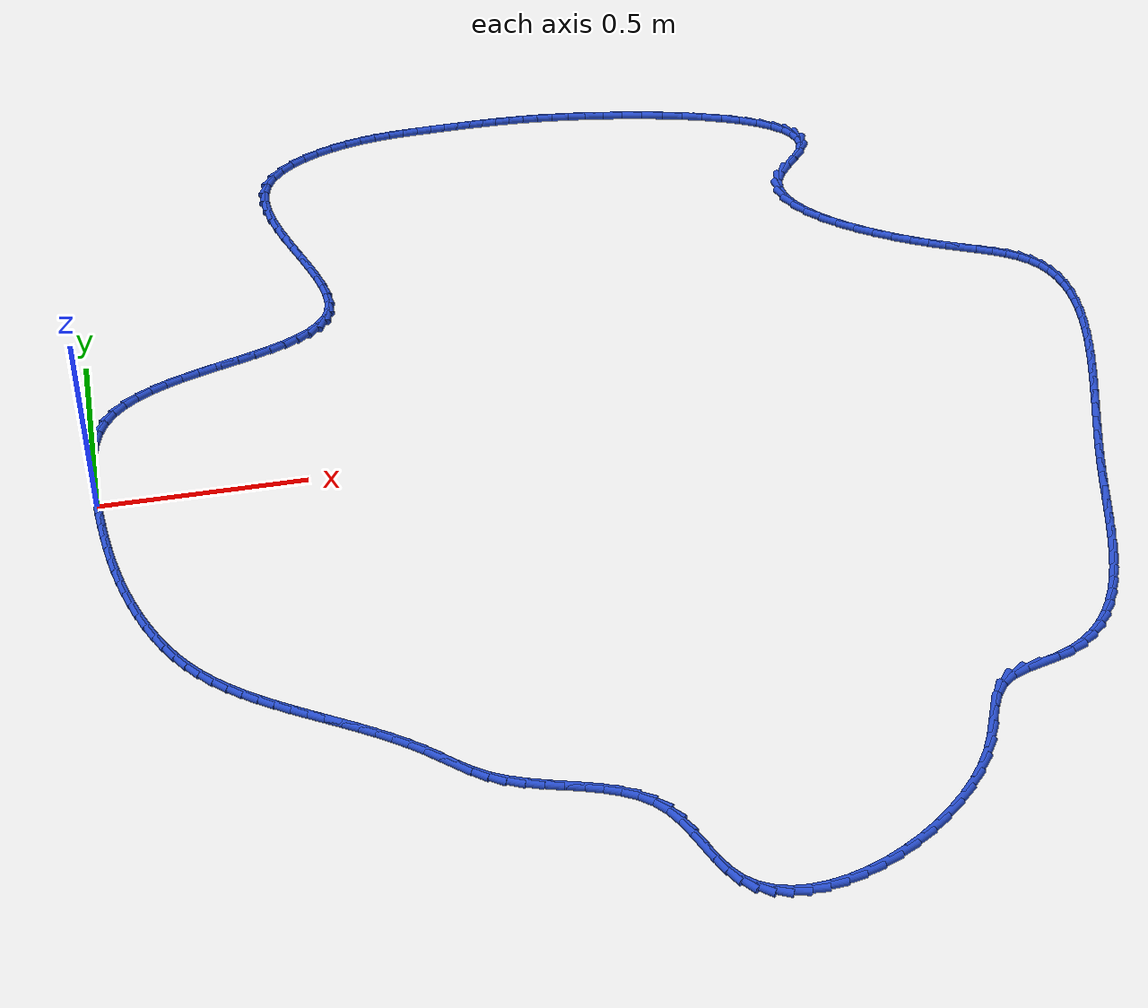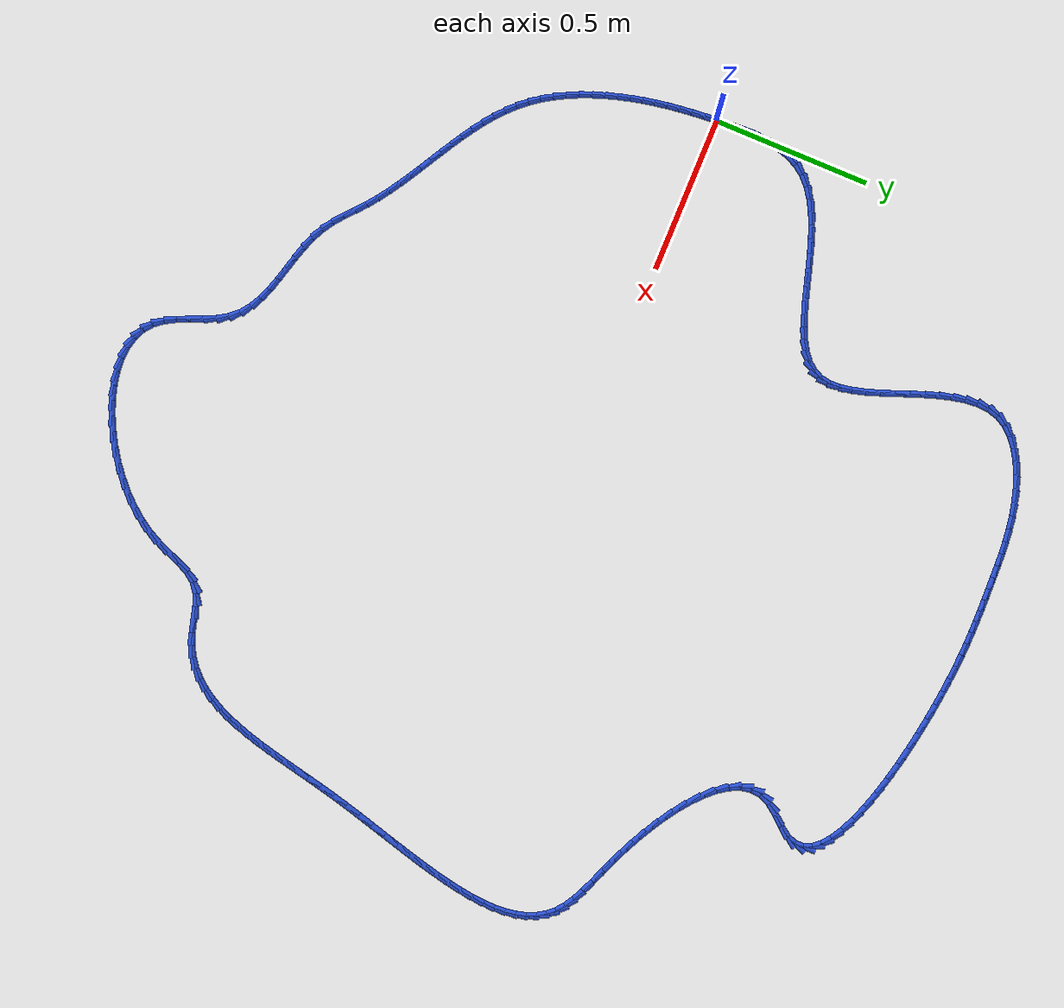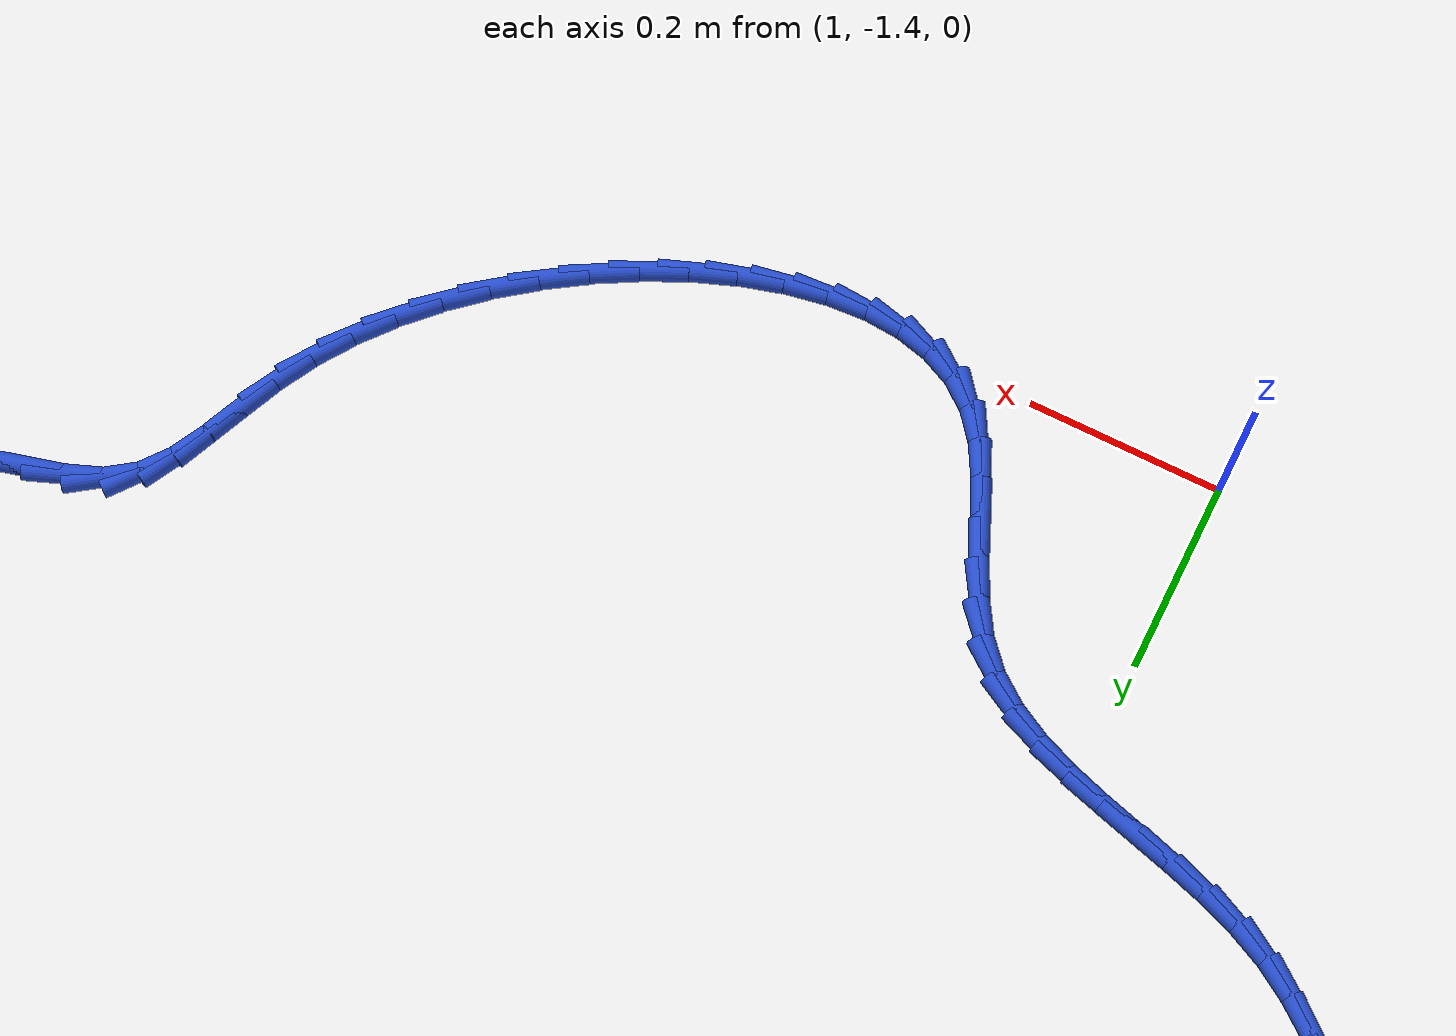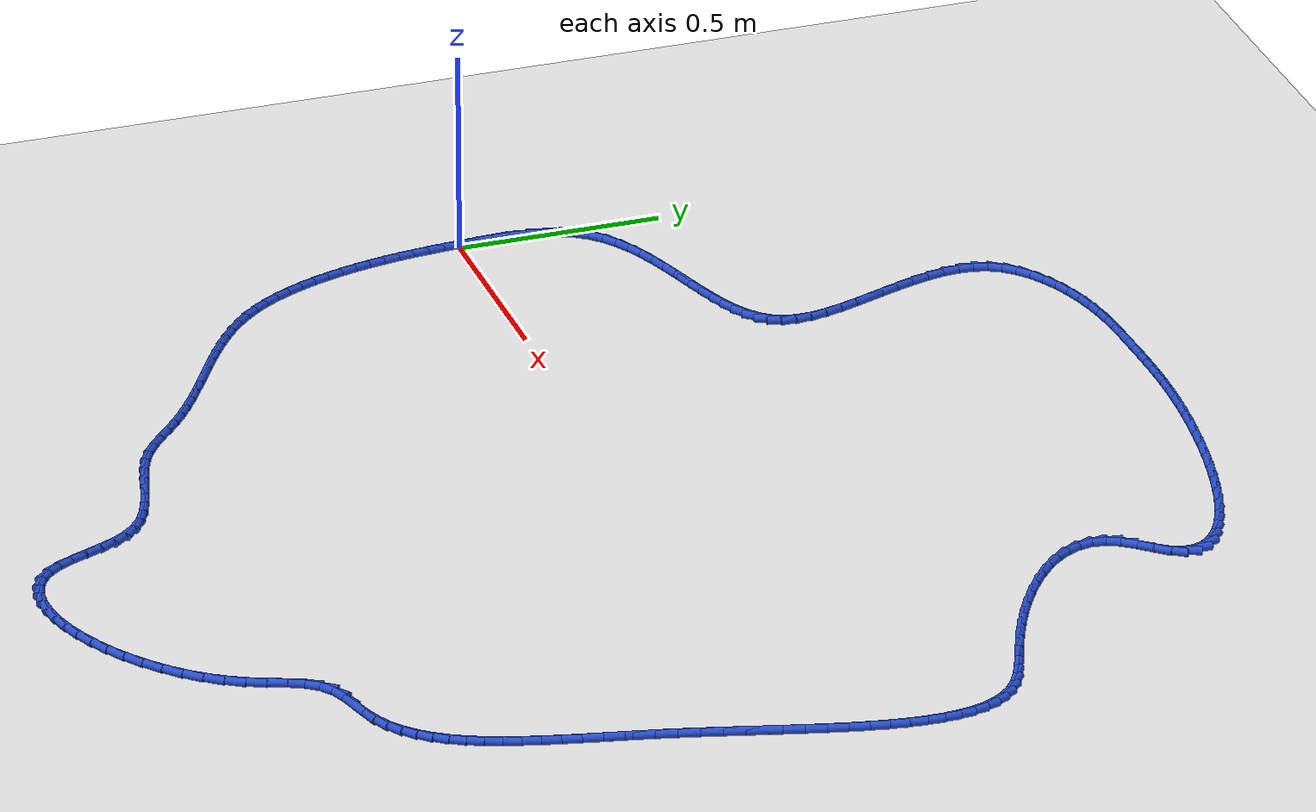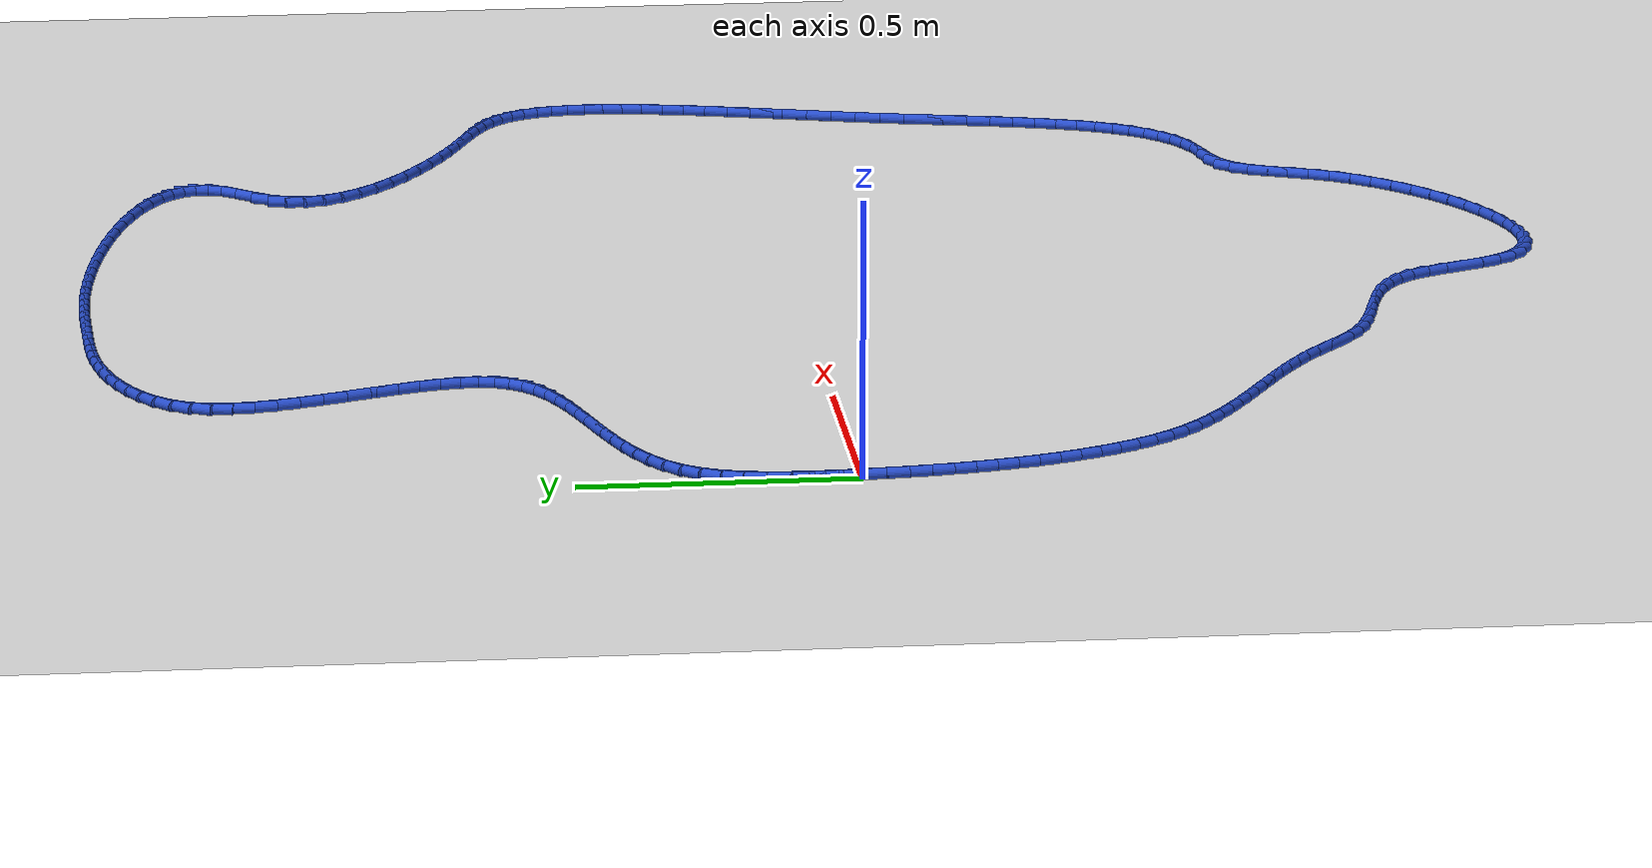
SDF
<sdf version="1.6">
 <world name="default">
  <light name="sun" type="directional">
   <pose>0 0 10 0 -0 0</pose>
   <diffuse>0.8 0.8 0.8 1</diffuse>
   <specular>0.2 0.2 0.2 1</specular>
   <attenuation>
    <range>1000</range>
    <constant>0.9</constant>
    <linear>0.01</linear>
    <quadratic>0.001</quadratic>
   </attenuation>
   <direction>-0.5 0.1 -0.9</direction>
  </light>
  <model name="ground_plane">
   <static>1</static>
   <link name="link">
    <collision name="collision">
     <geometry><plane><normal>0 0 1</normal><size>100 100</size></plane></geometry>
     <surface><friction><ode><mu>100</mu><mu2>50</mu2></ode></friction></surface>
    </collision>
    <visual name="visual">
     <cast_shadows>0</cast_shadows>
     <geometry><plane><normal>0 0 1</normal><size>100 100</size></plane></geometry>
     <material>
      <script><uri>file://media/materials/scripts/gazebo.material</uri><name>Gazebo/WhiteGlow</name></script>
     </material>
    </visual>
   </link>
  </model>
  <gravity>0 0 -9.8</gravity>
  <magnetic_field>6e-06 2.3e-05 -4.2e-05</magnetic_field>
  <atmosphere type="adiabatic"/>
  <physics name="default_physics" default="0" type="ode">
   <max_step_size>0.001</max_step_size>
   <real_time_factor>1</real_time_factor>
   <real_time_update_rate>1000</real_time_update_rate>
  </physics>
  <scene><ambient>0.4 0.4 0.4 1</ambient><background>0.7 0.7 0.7 1</background><shadows>1</shadows></scene>
  <spherical_coordinates>
   <surface_model>EARTH_WGS84</surface_model>
   <latitude_deg>0</latitude_deg>
   <longitude_deg>0</longitude_deg>
   <elevation>0</elevation>
   <heading_deg>0</heading_deg>
  </spherical_coordinates>
  <model name="line">
   <link name="link_0">
    <pose>-2.0383000842727483e-17 -1.1102230246251565e-16 0.01 0 1.57 -1.508984199646049</pose>
    <collision name="collision">
     <geometry><cylinder><radius>0.01</radius><length>0.08</length></cylinder></geometry>
    </collision>
    <visual name="visual">
     <material>
      <script><name>Gazebo/Blue</name><uri>file://media/materials/scripts/gazebo.material</uri></script>
     </material>
     <geometry><cylinder><radius>0.01</radius><length>0.08</length></cylinder></geometry>
    </visual>
   </link>
   <link name="link_1">
    <pose>-0.0025937557235531923 0.041908467589019074 0.01 0 1.57 -1.5369183679164307</pose>
    <collision name="collision">
     <geometry><cylinder><radius>0.01</radius><length>0.08</length></cylinder></geometry>
    </collision>
    <visual name="visual">
     <material>
      <script><name>Gazebo/Blue</name><uri>file://media/materials/scripts/gazebo.material</uri></script>
     </material>
     <geometry><cylinder><radius>0.01</radius><length>0.08</length></cylinder></geometry>
    </visual>
   </link>
   <link name="link_2">
    <pose>-0.004026922768987371 0.0841961012385936 0.01 0 1.57 1.5589588671000538</pose>
    <collision name="collision">
     <geometry><cylinder><radius>0.01</radius><length>0.08</length></cylinder></geometry>
    </collision>
    <visual name="visual">
     <material>
      <script><name>Gazebo/Blue</name><uri>file://media/materials/scripts/gazebo.material</uri></script>
     </material>
     <geometry><cylinder><radius>0.01</radius><length>0.08</length></cylinder></geometry>
    </visual>
   </link>
   <link name="link_3">
    <pose>-0.0035299012083987186 0.12618132087694997 0.01 0 1.57 1.4929850990292006</pose>
    <collision name="collision">
     <geometry><cylinder><radius>0.01</radius><length>0.08</length></cylinder></geometry>
    </collision>
    <visual name="visual">
     <material>
      <script><name>Gazebo/Blue</name><uri>file://media/materials/scripts/gazebo.material</uri></script>
     </material>
     <geometry><cylinder><radius>0.01</radius><length>0.08</length></cylinder></geometry>
    </visual>
   </link>
   <link name="link_4">
    <pose>-0.00033309111388339814 0.16718254643231467 0.01 0 1.57 1.4029216809968357</pose>
    <collision name="collision">
     <geometry><cylinder><radius>0.01</radius><length>0.08</length></cylinder></geometry>
    </collision>
    <visual name="visual">
     <material>
      <script><name>Gazebo/Blue</name><uri>file://media/materials/scripts/gazebo.material</uri></script>
     </material>
     <geometry><cylinder><radius>0.01</radius><length>0.08</length></cylinder></geometry>
    </visual>
   </link>
   <link name="link_5">
    <pose>0.00633310744246242 0.2065181978329144 0.01 0 1.57 1.2840926498506111</pose>
    <collision name="collision">
     <geometry><cylinder><radius>0.01</radius><length>0.08</length></cylinder></geometry>
    </collision>
    <visual name="visual">
     <material>
      <script><name>Gazebo/Blue</name><uri>file://media/materials/scripts/gazebo.material</uri></script>
     </material>
     <geometry><cylinder><radius>0.01</radius><length>0.08</length></cylinder></geometry>
    </visual>
   </link>
   <link name="link_6">
    <pose>0.01723829438854259 0.2435066950069756 0.01 0 1.57 1.1325771899493786</pose>
    <collision name="collision">
     <geometry><cylinder><radius>0.01</radius><length>0.08</length></cylinder></geometry>
    </collision>
    <visual name="visual">
     <material>
      <script><name>Gazebo/Blue</name><uri>file://media/materials/scripts/gazebo.material</uri></script>
     </material>
     <geometry><cylinder><radius>0.01</radius><length>0.08</length></cylinder></geometry>
    </visual>
   </link>
   <link name="link_7">
    <pose>0.03315206965226094 0.2774664578827249 0.01 0 1.57 0.9494726755291081</pose>
    <collision name="collision">
     <geometry><cylinder><radius>0.01</radius><length>0.08</length></cylinder></geometry>
    </collision>
    <visual name="visual">
     <material>
      <script><name>Gazebo/Blue</name><uri>file://media/materials/scripts/gazebo.material</uri></script>
     </material>
     <geometry><cylinder><radius>0.01</radius><length>0.08</length></cylinder></geometry>
    </visual>
   </link>
   <link name="link_8">
    <pose>0.05482023807800502 0.30773310252756725 0.01 0 1.57 0.7664684722568968</pose>
    <collision name="collision">
     <geometry><cylinder><radius>0.01</radius><length>0.08</length></cylinder></geometry>
    </collision>
    <visual name="visual">
     <material>
      <script><name>Gazebo/Blue</name><uri>file://media/materials/scripts/gazebo.material</uri></script>
     </material>
     <geometry><cylinder><radius>0.01</radius><length>0.08</length></cylinder></geometry>
    </visual>
   </link>
   <link name="link_9">
    <pose>0.08226925402855513 0.33416210244044053 0.01 0 1.57 0.6179066574830141</pose>
    <collision name="collision">
     <geometry><cylinder><radius>0.01</radius><length>0.08</length></cylinder></geometry>
    </collision>
    <visual name="visual">
     <material>
      <script><name>Gazebo/Blue</name><uri>file://media/materials/scripts/gazebo.material</uri></script>
     </material>
     <geometry><cylinder><radius>0.01</radius><length>0.08</length></cylinder></geometry>
    </visual>
   </link>
   <link name="link_10">
    <pose>0.11469524535313261 0.35720898828255493 0.01 0 1.57 0.5038825935117731</pose>
    <collision name="collision">
     <geometry><cylinder><radius>0.01</radius><length>0.08</length></cylinder></geometry>
    </collision>
    <visual name="visual">
     <material>
      <script><name>Gazebo/Blue</name><uri>file://media/materials/scripts/gazebo.material</uri></script>
     </material>
     <geometry><cylinder><radius>0.01</radius><length>0.08</length></cylinder></geometry>
    </visual>
   </link>
   <link name="link_11">
    <pose>0.15124820629704872 0.3773626303700579 0.01 0 1.57 0.4192109456956508</pose>
    <collision name="collision">
     <geometry><cylinder><radius>0.01</radius><length>0.08</length></cylinder></geometry>
    </collision>
    <visual name="visual">
     <material>
      <script><name>Gazebo/Blue</name><uri>file://media/materials/scripts/gazebo.material</uri></script>
     </material>
     <geometry><cylinder><radius>0.01</radius><length>0.08</length></cylinder></geometry>
    </visual>
   </link>
   <link name="link_12">
    <pose>0.19107813110561453 0.3951118990190969 0.01 0 1.57 0.3585099443431421</pose>
    <collision name="collision">
     <geometry><cylinder><radius>0.01</radius><length>0.08</length></cylinder></geometry>
    </collision>
    <visual name="visual">
     <material>
      <script><name>Gazebo/Blue</name><uri>file://media/materials/scripts/gazebo.material</uri></script>
     </material>
     <geometry><cylinder><radius>0.01</radius><length>0.08</length></cylinder></geometry>
    </visual>
   </link>
   <link name="link_13">
    <pose>0.23333501402414158 0.41094566454581993 0.01 0 1.57 0.3175531777257455</pose>
    <collision name="collision">
     <geometry><cylinder><radius>0.01</radius><length>0.08</length></cylinder></geometry>
    </collision>
    <visual name="visual">
     <material>
      <script><name>Gazebo/Blue</name><uri>file://media/materials/scripts/gazebo.material</uri></script>
     </material>
     <geometry><cylinder><radius>0.01</radius><length>0.08</length></cylinder></geometry>
    </visual>
   </link>
   <link name="link_14">
    <pose>0.277168849297941 0.42535279726637454 0.01 0 1.57 0.29353770409655716</pose>
    <collision name="collision">
     <geometry><cylinder><radius>0.01</radius><length>0.08</length></cylinder></geometry>
    </collision>
    <visual name="visual">
     <material>
      <script><name>Gazebo/Blue</name><uri>file://media/materials/scripts/gazebo.material</uri></script>
     </material>
     <geometry><cylinder><radius>0.01</radius><length>0.08</length></cylinder></geometry>
    </visual>
   </link>
   <link name="link_15">
    <pose>0.32172963117232395 0.43882216749690806 0.01 0 1.57 0.2850271375050466</pose>
    <collision name="collision">
     <geometry><cylinder><radius>0.01</radius><length>0.08</length></cylinder></geometry>
    </collision>
    <visual name="visual">
     <material>
      <script><name>Gazebo/Blue</name><uri>file://media/materials/scripts/gazebo.material</uri></script>
     </material>
     <geometry><cylinder><radius>0.01</radius><length>0.08</length></cylinder></geometry>
    </visual>
   </link>
   <link name="link_16">
    <pose>0.36616735389260185 0.45184264555356823 0.01 0 1.57 0.29190123542418794</pose>
    <collision name="collision">
     <geometry><cylinder><radius>0.01</radius><length>0.08</length></cylinder></geometry>
    </collision>
    <visual name="visual">
     <material>
      <script><name>Gazebo/Blue</name><uri>file://media/materials/scripts/gazebo.material</uri></script>
     </material>
     <geometry><cylinder><radius>0.01</radius><length>0.08</length></cylinder></geometry>
    </visual>
   </link>
   <link name="link_17">
    <pose>0.4096320117040857 0.46490310175250293 0.01 0 1.57 0.3154431690553602</pose>
    <collision name="collision">
     <geometry><cylinder><radius>0.01</radius><length>0.08</length></cylinder></geometry>
    </collision>
    <visual name="visual">
     <material>
      <script><name>Gazebo/Blue</name><uri>file://media/materials/scripts/gazebo.material</uri></script>
     </material>
     <geometry><cylinder><radius>0.01</radius><length>0.08</length></cylinder></geometry>
    </visual>
   </link>
   <link name="link_18">
    <pose>0.45127359885208707 0.47849240640985946 0.01 0 1.57 0.3586318935152991</pose>
    <collision name="collision">
     <geometry><cylinder><radius>0.01</radius><length>0.08</length></cylinder></geometry>
    </collision>
    <visual name="visual">
     <material>
      <script><name>Gazebo/Blue</name><uri>file://media/materials/scripts/gazebo.material</uri></script>
     </material>
     <geometry><cylinder><radius>0.01</radius><length>0.08</length></cylinder></geometry>
    </visual>
   </link>
   <link name="link_19">
    <pose>0.4902421095819172 0.49309942984178573 0.01 0 1.57 0.42667551971940476</pose>
    <collision name="collision">
     <geometry><cylinder><radius>0.01</radius><length>0.08</length></cylinder></geometry>
    </collision>
    <visual name="visual">
     <material>
      <script><name>Gazebo/Blue</name><uri>file://media/materials/scripts/gazebo.material</uri></script>
     </material>
     <geometry><cylinder><radius>0.01</radius><length>0.08</length></cylinder></geometry>
    </visual>
   </link>
   <link name="link_20">
    <pose>0.5256875381388871 0.5092130423644292 0.01 0 1.57 0.5276791146542511</pose>
    <collision name="collision">
     <geometry><cylinder><radius>0.01</radius><length>0.08</length></cylinder></geometry>
    </collision>
    <visual name="visual">
     <material>
      <script><name>Gazebo/Blue</name><uri>file://media/materials/scripts/gazebo.material</uri></script>
     </material>
     <geometry><cylinder><radius>0.01</radius><length>0.08</length></cylinder></geometry>
    </visual>
   </link>
   <link name="link_21">
    <pose>0.5567598787683082 0.5273221142939375 0.01 0 1.57 0.6727090961939625</pose>
    <collision name="collision">
     <geometry><cylinder><radius>0.01</radius><length>0.08</length></cylinder></geometry>
    </collision>
    <visual name="visual">
     <material>
      <script><name>Gazebo/Blue</name><uri>file://media/materials/scripts/gazebo.material</uri></script>
     </material>
     <geometry><cylinder><radius>0.01</radius><length>0.08</length></cylinder></geometry>
    </visual>
   </link>
   <link name="link_22">
    <pose>0.582609125715492 0.5479155159464584 0.01 0 1.57 0.8726292501060373</pose>
    <collision name="collision">
     <geometry><cylinder><radius>0.01</radius><length>0.08</length></cylinder></geometry>
    </collision>
    <visual name="visual">
     <material>
      <script><name>Gazebo/Blue</name><uri>file://media/materials/scripts/gazebo.material</uri></script>
     </material>
     <geometry><cylinder><radius>0.01</radius><length>0.08</length></cylinder></geometry>
    </visual>
   </link>
   <link name="link_23">
    <pose>0.6023852732257492 0.5714821176381393 0.01 0 1.57 1.126886971013885</pose>
    <collision name="collision">
     <geometry><cylinder><radius>0.01</radius><length>0.08</length></cylinder></geometry>
    </collision>
    <visual name="visual">
     <material>
      <script><name>Gazebo/Blue</name><uri>file://media/materials/scripts/gazebo.material</uri></script>
     </material>
     <geometry><cylinder><radius>0.01</radius><length>0.08</length></cylinder></geometry>
    </visual>
   </link>
   <link name="link_24">
    <pose>0.6152390025890027 0.5985104418861228 0.01 0 1.57 1.3922145638857792</pose>
    <collision name="collision">
     <geometry><cylinder><radius>0.01</radius><length>0.08</length></cylinder></geometry>
    </collision>
    <visual name="visual">
     <material>
      <script><name>Gazebo/Blue</name><uri>file://media/materials/scripts/gazebo.material</uri></script>
     </material>
     <geometry><cylinder><radius>0.01</radius><length>0.08</length></cylinder></geometry>
    </visual>
   </link>
   <link name="link_25">
    <pose>0.6207880981786935 0.6292525520532252 0.01 0 1.57 -1.5455949504341018</pose>
    <collision name="collision">
     <geometry><cylinder><radius>0.01</radius><length>0.08</length></cylinder></geometry>
    </collision>
    <visual name="visual">
     <material>
      <script><name>Gazebo/Blue</name><uri>file://media/materials/scripts/gazebo.material</uri></script>
     </material>
     <geometry><cylinder><radius>0.01</radius><length>0.08</length></cylinder></geometry>
    </visual>
   </link>
   <link name="link_26">
    <pose>0.6199295475775028 0.6633129471428305 0.01 0 1.57 -1.4054724043046753</pose>
    <collision name="collision">
     <geometry><cylinder><radius>0.01</radius><length>0.08</length></cylinder></geometry>
    </collision>
    <visual name="visual">
     <material>
      <script><name>Gazebo/Blue</name><uri>file://media/materials/scripts/gazebo.material</uri></script>
     </material>
     <geometry><cylinder><radius>0.01</radius><length>0.08</length></cylinder></geometry>
    </visual>
   </link>
   <link name="link_27">
    <pose>0.6137773525054828 0.7001862682250095 0.01 0 1.57 -1.312969559625191</pose>
    <collision name="collision">
     <geometry><cylinder><radius>0.01</radius><length>0.08</length></cylinder></geometry>
    </collision>
    <visual name="visual">
     <material>
      <script><name>Gazebo/Blue</name><uri>file://media/materials/scripts/gazebo.material</uri></script>
     </material>
     <geometry><cylinder><radius>0.01</radius><length>0.08</length></cylinder></geometry>
    </visual>
   </link>
   <link name="link_28">
    <pose>0.6034455146826864 0.7393671563698321 0.01 0 1.57 -1.2548445960010377</pose>
    <collision name="collision">
     <geometry><cylinder><radius>0.01</radius><length>0.08</length></cylinder></geometry>
    </collision>
    <visual name="visual">
     <material>
      <script><name>Gazebo/Blue</name><uri>file://media/materials/scripts/gazebo.material</uri></script>
     </material>
     <geometry><cylinder><radius>0.01</radius><length>0.08</length></cylinder></geometry>
    </visual>
   </link>
   <link name="link_29">
    <pose>0.5900480358291662 0.7803502526473688 0.01 0 1.57 -1.2225561777159923</pose>
    <collision name="collision">
     <geometry><cylinder><radius>0.01</radius><length>0.08</length></cylinder></geometry>
    </collision>
    <visual name="visual">
     <material>
      <script><name>Gazebo/Blue</name><uri>file://media/materials/scripts/gazebo.material</uri></script>
     </material>
     <geometry><cylinder><radius>0.01</radius><length>0.08</length></cylinder></geometry>
    </visual>
   </link>
   <link name="link_30">
    <pose>0.5746989176649747 0.8226301981276901 0.01 0 1.57 -1.21131409168786</pose>
    <collision name="collision">
     <geometry><cylinder><radius>0.01</radius><length>0.08</length></cylinder></geometry>
    </collision>
    <visual name="visual">
     <material>
      <script><name>Gazebo/Blue</name><uri>file://media/materials/scripts/gazebo.material</uri></script>
     </material>
     <geometry><cylinder><radius>0.01</radius><length>0.08</length></cylinder></geometry>
    </visual>
   </link>
   <link name="link_31">
    <pose>0.5585121619101648 0.865701633880866 0.01 0 1.57 -1.219095044279078</pose>
    <collision name="collision">
     <geometry><cylinder><radius>0.01</radius><length>0.08</length></cylinder></geometry>
    </collision>
    <visual name="visual">
     <material>
      <script><name>Gazebo/Blue</name><uri>file://media/materials/scripts/gazebo.material</uri></script>
     </material>
     <geometry><cylinder><radius>0.01</radius><length>0.08</length></cylinder></geometry>
    </visual>
   </link>
   <link name="link_32">
    <pose>0.5426017702847892 0.9090592009769675 0.01 0 1.57 -1.2461157242385992</pose>
    <collision name="collision">
     <geometry><cylinder><radius>0.01</radius><length>0.08</length></cylinder></geometry>
    </collision>
    <visual name="visual">
     <material>
      <script><name>Gazebo/Blue</name><uri>file://media/materials/scripts/gazebo.material</uri></script>
     </material>
     <geometry><cylinder><radius>0.01</radius><length>0.08</length></cylinder></geometry>
    </visual>
   </link>
   <link name="link_33">
    <pose>0.5280817445089002 0.9521975404860645 0.01 0 1.57 -1.2947336127291564</pose>
    <collision name="collision">
     <geometry><cylinder><radius>0.01</radius><length>0.08</length></cylinder></geometry>
    </collision>
    <visual name="visual">
     <material>
      <script><name>Gazebo/Blue</name><uri>file://media/materials/scripts/gazebo.material</uri></script>
     </material>
     <geometry><cylinder><radius>0.01</radius><length>0.08</length></cylinder></geometry>
    </visual>
   </link>
   <link name="link_34">
    <pose>0.516066086302551 0.9946112934782274 0.01 0 1.57 -1.3696556799582007</pose>
    <collision name="collision">
     <geometry><cylinder><radius>0.01</radius><length>0.08</length></cylinder></geometry>
    </collision>
    <visual name="visual">
     <material>
      <script><name>Gazebo/Blue</name><uri>file://media/materials/scripts/gazebo.material</uri></script>
     </material>
     <geometry><cylinder><radius>0.01</radius><length>0.08</length></cylinder></geometry>
    </visual>
   </link>
   <link name="link_35">
    <pose>0.5076687973857938 1.035795101023527 0.01 0 1.57 -1.4781583871688446</pose>
    <collision name="collision">
     <geometry><cylinder><radius>0.01</radius><length>0.08</length></cylinder></geometry>
    </collision>
    <visual name="visual">
     <material>
      <script><name>Gazebo/Blue</name><uri>file://media/materials/scripts/gazebo.material</uri></script>
     </material>
     <geometry><cylinder><radius>0.01</radius><length>0.08</length></cylinder></geometry>
    </visual>
   </link>
   <link name="link_36">
    <pose>0.5040038794786816 1.0752436041920332 0.01 0 1.57 1.5122344618841372</pose>
    <collision name="collision">
     <geometry><cylinder><radius>0.01</radius><length>0.08</length></cylinder></geometry>
    </collision>
    <visual name="visual">
     <material>
      <script><name>Gazebo/Blue</name><uri>file://media/materials/scripts/gazebo.material</uri></script>
     </material>
     <geometry><cylinder><radius>0.01</radius><length>0.08</length></cylinder></geometry>
    </visual>
   </link>
   <link name="link_37">
    <pose>0.506185334301267 1.1124514440538165 0.01 0 1.57 1.3114944554749692</pose>
    <collision name="collision">
     <geometry><cylinder><radius>0.01</radius><length>0.08</length></cylinder></geometry>
    </collision>
    <visual name="visual">
     <material>
      <script><name>Gazebo/Blue</name><uri>file://media/materials/scripts/gazebo.material</uri></script>
     </material>
     <geometry><cylinder><radius>0.01</radius><length>0.08</length></cylinder></geometry>
    </visual>
   </link>
   <link name="link_38">
    <pose>0.5153271635736028 1.146913261678948 0.01 0 1.57 1.0700592484595162</pose>
    <collision name="collision">
     <geometry><cylinder><radius>0.01</radius><length>0.08</length></cylinder></geometry>
    </collision>
    <visual name="visual">
     <material>
      <script><name>Gazebo/Blue</name><uri>file://media/materials/scripts/gazebo.material</uri></script>
     </material>
     <geometry><cylinder><radius>0.01</radius><length>0.08</length></cylinder></geometry>
    </visual>
   </link>
   <link name="link_39">
    <pose>0.5324222235210633 1.1781508125017197 0.01 0 1.57 0.8473275931144263</pose>
    <collision name="collision">
     <geometry><cylinder><radius>0.01</radius><length>0.08</length></cylinder></geometry>
    </collision>
    <visual name="visual">
     <material>
      <script><name>Gazebo/Blue</name><uri>file://media/materials/scripts/gazebo.material</uri></script>
     </material>
     <geometry><cylinder><radius>0.01</radius><length>0.08</length></cylinder></geometry>
    </visual>
   </link>
   <link name="link_40">
    <pose>0.5570259686857548 1.2060075662131464 0.01 0 1.57 0.6737259484942114</pose>
    <collision name="collision">
     <geometry><cylinder><radius>0.01</radius><length>0.08</length></cylinder></geometry>
    </collision>
    <visual name="visual">
     <material>
      <script><name>Gazebo/Blue</name><uri>file://media/materials/scripts/gazebo.material</uri></script>
     </material>
     <geometry><cylinder><radius>0.01</radius><length>0.08</length></cylinder></geometry>
    </visual>
   </link>
   <link name="link_41">
    <pose>0.5877524973840397 1.2305376835880188 0.01 0 1.57 0.5402752953222988</pose>
    <collision name="collision">
     <geometry><cylinder><radius>0.01</radius><length>0.08</length></cylinder></geometry>
    </collision>
    <visual name="visual">
     <material>
      <script><name>Gazebo/Blue</name><uri>file://media/materials/scripts/gazebo.material</uri></script>
     </material>
     <geometry><cylinder><radius>0.01</radius><length>0.08</length></cylinder></geometry>
    </visual>
   </link>
   <link name="link_42">
    <pose>0.6231995774989652 1.2517989804220448 0.01 0 1.57 0.43577467851882024</pose>
    <collision name="collision">
     <geometry><cylinder><radius>0.01</radius><length>0.08</length></cylinder></geometry>
    </collision>
    <visual name="visual">
     <material>
      <script><name>Gazebo/Blue</name><uri>file://media/materials/scripts/gazebo.material</uri></script>
     </material>
     <geometry><cylinder><radius>0.01</radius><length>0.08</length></cylinder></geometry>
    </visual>
   </link>
   <link name="link_43">
    <pose>0.661964976913579 1.2698492725109305 0.01 0 1.57 0.35102345976377064</pose>
    <collision name="collision">
     <geometry><cylinder><radius>0.01</radius><length>0.08</length></cylinder></geometry>
    </collision>
    <visual name="visual">
     <material>
      <script><name>Gazebo/Blue</name><uri>file://media/materials/scripts/gazebo.material</uri></script>
     </material>
     <geometry><cylinder><radius>0.01</radius><length>0.08</length></cylinder></geometry>
    </visual>
   </link>
   <link name="link_44">
    <pose>0.702646463510929 1.2847463756503834 0.01 0 1.57 0.2790111882744085</pose>
    <collision name="collision">
     <geometry><cylinder><radius>0.01</radius><length>0.08</length></cylinder></geometry>
    </collision>
    <visual name="visual">
     <material>
      <script><name>Gazebo/Blue</name><uri>file://media/materials/scripts/gazebo.material</uri></script>
     </material>
     <geometry><cylinder><radius>0.01</radius><length>0.08</length></cylinder></geometry>
    </visual>
   </link>
   <link name="link_45">
    <pose>0.7438486055359255 1.2965501323981472 0.01 0 1.57 0.21504136879132027</pose>
    <collision name="collision">
     <geometry><cylinder><radius>0.01</radius><length>0.08</length></cylinder></geometry>
    </collision>
    <visual name="visual">
     <material>
      <script><name>Gazebo/Blue</name><uri>file://media/materials/scripts/gazebo.material</uri></script>
     </material>
     <geometry><cylinder><radius>0.01</radius><length>0.08</length></cylinder></geometry>
    </visual>
   </link>
   <link name="link_46">
    <pose>0.7846531452208726 1.3054626009972259 0.01 0 1.57 0.158971176484876</pose>
    <collision name="collision">
     <geometry><cylinder><radius>0.01</radius><length>0.08</length></cylinder></geometry>
    </collision>
    <visual name="visual">
     <material>
      <script><name>Gazebo/Blue</name><uri>file://media/materials/scripts/gazebo.material</uri></script>
     </material>
     <geometry><cylinder><radius>0.01</radius><length>0.08</length></cylinder></geometry>
    </visual>
   </link>
   <link name="link_47">
    <pose>0.8249242113704589 1.3119190201352249 0.01 0 1.57 0.11187657022212875</pose>
    <collision name="collision">
     <geometry><cylinder><radius>0.01</radius><length>0.08</length></cylinder></geometry>
    </collision>
    <visual name="visual">
     <material>
      <script><name>Gazebo/Blue</name><uri>file://media/materials/scripts/gazebo.material</uri></script>
     </material>
     <geometry><cylinder><radius>0.01</radius><length>0.08</length></cylinder></geometry>
    </visual>
   </link>
   <link name="link_48">
    <pose>0.8645984940612368 1.3163762544711408 0.01 0 1.57 0.07457564666549331</pose>
    <collision name="collision">
     <geometry><cylinder><radius>0.01</radius><length>0.08</length></cylinder></geometry>
    </collision>
    <visual name="visual">
     <material>
      <script><name>Gazebo/Blue</name><uri>file://media/materials/scripts/gazebo.material</uri></script>
     </material>
     <geometry><cylinder><radius>0.01</radius><length>0.08</length></cylinder></geometry>
    </visual>
   </link>
   <link name="link_49">
    <pose>0.9036126833697584 1.3192911686639732 0.01 0 1.57 0.04774173483753255</pose>
    <collision name="collision">
     <geometry><cylinder><radius>0.01</radius><length>0.08</length></cylinder></geometry>
    </collision>
    <visual name="visual">
     <material>
      <script><name>Gazebo/Blue</name><uri>file://media/materials/scripts/gazebo.material</uri></script>
     </material>
     <geometry><cylinder><radius>0.01</radius><length>0.08</length></cylinder></geometry>
    </visual>
   </link>
   <link name="link_50">
    <pose>0.941903469372576 1.32112062737272 0.01 0 1.57 0.03200872990443709</pose>
    <collision name="collision">
     <geometry><cylinder><radius>0.01</radius><length>0.08</length></cylinder></geometry>
    </collision>
    <visual name="visual">
     <material>
      <script><name>Gazebo/Blue</name><uri>file://media/materials/scripts/gazebo.material</uri></script>
     </material>
     <geometry><cylinder><radius>0.01</radius><length>0.08</length></cylinder></geometry>
    </visual>
   </link>
   <link name="link_51">
    <pose>0.9794075421462419 1.3223214952563795 0.01 0 1.57 0.02745105983898128</pose>
    <collision name="collision">
     <geometry><cylinder><radius>0.01</radius><length>0.08</length></cylinder></geometry>
    </collision>
    <visual name="visual">
     <material>
      <script><name>Gazebo/Blue</name><uri>file://media/materials/scripts/gazebo.material</uri></script>
     </material>
     <geometry><cylinder><radius>0.01</radius><length>0.08</length></cylinder></geometry>
    </visual>
   </link>
   <link name="link_52">
    <pose>1.0160799750475469 1.3233284453517702 0.01 0 1.57 0.0255893068580838</pose>
    <collision name="collision">
     <geometry><cylinder><radius>0.01</radius><length>0.08</length></cylinder></geometry>
    </collision>
    <visual name="visual">
     <material>
      <script><name>Gazebo/Blue</name><uri>file://media/materials/scripts/gazebo.material</uri></script>
     </material>
     <geometry><cylinder><radius>0.01</radius><length>0.08</length></cylinder></geometry>
    </visual>
   </link>
   <link name="link_53">
    <pose>1.0521447619207036 1.324251519738889 0.01 0 1.57 0.019590090633233595</pose>
    <collision name="collision">
     <geometry><cylinder><radius>0.01</radius><length>0.08</length></cylinder></geometry>
    </collision>
    <visual name="visual">
     <material>
      <script><name>Gazebo/Blue</name><uri>file://media/materials/scripts/gazebo.material</uri></script>
     </material>
     <geometry><cylinder><radius>0.01</radius><length>0.08</length></cylinder></geometry>
    </visual>
   </link>
   <link name="link_54">
    <pose>1.088029812200985 1.3249546010694535 0.01 0 1.57 0.009431579210391387</pose>
    <collision name="collision">
     <geometry><cylinder><radius>0.01</radius><length>0.08</length></cylinder></geometry>
    </collision>
    <visual name="visual">
     <material>
      <script><name>Gazebo/Blue</name><uri>file://media/materials/scripts/gazebo.material</uri></script>
     </material>
     <geometry><cylinder><radius>0.01</radius><length>0.08</length></cylinder></geometry>
    </visual>
   </link>
   <link name="link_55">
    <pose>1.1241681047701428 1.3252954523451805 0.01 0 1.57 -0.00444309195493434</pose>
    <collision name="collision">
     <geometry><cylinder><radius>0.01</radius><length>0.08</length></cylinder></geometry>
    </collision>
    <visual name="visual">
     <material>
      <script><name>Gazebo/Blue</name><uri>file://media/materials/scripts/gazebo.material</uri></script>
     </material>
     <geometry><cylinder><radius>0.01</radius><length>0.08</length></cylinder></geometry>
    </visual>
   </link>
   <link name="link_56">
    <pose>1.1609926185099289 1.3251318365677875 0.01 0 1.57 -0.02135259291994002</pose>
    <collision name="collision">
     <geometry><cylinder><radius>0.01</radius><length>0.08</length></cylinder></geometry>
    </collision>
    <visual name="visual">
     <material>
      <script><name>Gazebo/Blue</name><uri>file://media/materials/scripts/gazebo.material</uri></script>
     </material>
     <geometry><cylinder><radius>0.01</radius><length>0.08</length></cylinder></geometry>
    </visual>
   </link>
   <link name="link_57">
    <pose>1.1989363323020936 1.324321516738992 0.01 0 1.57 -0.04046971935433926</pose>
    <collision name="collision">
     <geometry><cylinder><radius>0.01</radius><length>0.08</length></cylinder></geometry>
    </collision>
    <visual name="visual">
     <material>
      <script><name>Gazebo/Blue</name><uri>file://media/materials/scripts/gazebo.material</uri></script>
     </material>
     <geometry><cylinder><radius>0.01</radius><length>0.08</length></cylinder></geometry>
    </visual>
   </link>
   <link name="link_58">
    <pose>1.2384322250283883 1.3227222558605107 0.01 0 1.57 -0.06092678608826884</pose>
    <collision name="collision">
     <geometry><cylinder><radius>0.01</radius><length>0.08</length></cylinder></geometry>
    </collision>
    <visual name="visual">
     <material>
      <script><name>Gazebo/Blue</name><uri>file://media/materials/scripts/gazebo.material</uri></script>
     </material>
     <geometry><cylinder><radius>0.01</radius><length>0.08</length></cylinder></geometry>
    </visual>
   </link>
   <link name="link_59">
    <pose>1.2799132755705658 1.3201918169340614 0.01 0 1.57 -0.08191018645160461</pose>
    <collision name="collision">
     <geometry><cylinder><radius>0.01</radius><length>0.08</length></cylinder></geometry>
    </collision>
    <visual name="visual">
     <material>
      <script><name>Gazebo/Blue</name><uri>file://media/materials/scripts/gazebo.material</uri></script>
     </material>
     <geometry><cylinder><radius>0.01</radius><length>0.08</length></cylinder></geometry>
    </visual>
   </link>
   <link name="link_60">
    <pose>1.3238124628103765 1.3165879629613617 0.01 0 1.57 -0.10272747933632816</pose>
    <collision name="collision">
     <geometry><cylinder><radius>0.01</radius><length>0.08</length></cylinder></geometry>
    </collision>
    <visual name="visual">
     <material>
      <script><name>Gazebo/Blue</name><uri>file://media/materials/scripts/gazebo.material</uri></script>
     </material>
     <geometry><cylinder><radius>0.01</radius><length>0.08</length></cylinder></geometry>
    </visual>
   </link>
   <link name="link_61">
    <pose>1.3705627656295716 1.3117684569441284 0.01 0 1.57 -0.12289369342704996</pose>
    <collision name="collision">
     <geometry><cylinder><radius>0.01</radius><length>0.08</length></cylinder></geometry>
    </collision>
    <visual name="visual">
     <material>
      <script><name>Gazebo/Blue</name><uri>file://media/materials/scripts/gazebo.material</uri></script>
     </material>
     <geometry><cylinder><radius>0.01</radius><length>0.08</length></cylinder></geometry>
    </visual>
   </link>
   <link name="link_62">
    <pose>1.4204952045015808 1.305600995031575 0.01 0 1.57 -0.14285486224246896</pose>
    <collision name="collision">
     <geometry><cylinder><radius>0.01</radius><length>0.08</length></cylinder></geometry>
    </collision>
    <visual name="visual">
     <material>
      <script><name>Gazebo/Blue</name><uri>file://media/materials/scripts/gazebo.material</uri></script>
     </material>
     <geometry><cylinder><radius>0.01</radius><length>0.08</length></cylinder></geometry>
    </visual>
   </link>
   <link name="link_63">
    <pose>1.473087429432464 1.2980364117315932 0.01 0 1.57 -0.1636919185847594</pose>
    <collision name="collision">
     <geometry><cylinder><radius>0.01</radius><length>0.08</length></cylinder></geometry>
    </collision>
    <visual name="visual">
     <material>
      <script><name>Gazebo/Blue</name><uri>file://media/materials/scripts/gazebo.material</uri></script>
     </material>
     <geometry><cylinder><radius>0.01</radius><length>0.08</length></cylinder></geometry>
    </visual>
   </link>
   <link name="link_64">
    <pose>1.5273917203938736 1.289066982600064 0.01 0 1.57 -0.18634617327038</pose>
    <collision name="collision">
     <geometry><cylinder><radius>0.01</radius><length>0.08</length></cylinder></geometry>
    </collision>
    <visual name="visual">
     <material>
      <script><name>Gazebo/Blue</name><uri>file://media/materials/scripts/gazebo.material</uri></script>
     </material>
     <geometry><cylinder><radius>0.01</radius><length>0.08</length></cylinder></geometry>
    </visual>
   </link>
   <link name="link_65">
    <pose>1.5824572396208434 1.2786852869337584 0.01 0 1.57 -0.21182949814616803</pose>
    <collision name="collision">
     <geometry><cylinder><radius>0.01</radius><length>0.08</length></cylinder></geometry>
    </collision>
    <visual name="visual">
     <material>
      <script><name>Gazebo/Blue</name><uri>file://media/materials/scripts/gazebo.material</uri></script>
     </material>
     <geometry><cylinder><radius>0.01</radius><length>0.08</length></cylinder></geometry>
    </visual>
   </link>
   <link name="link_66">
    <pose>1.6373331493484085 1.2668839040294477 0.01 0 1.57 -0.24137830240991728</pose>
    <collision name="collision">
     <geometry><cylinder><radius>0.01</radius><length>0.08</length></cylinder></geometry>
    </collision>
    <visual name="visual">
     <material>
      <script><name>Gazebo/Blue</name><uri>file://media/materials/scripts/gazebo.material</uri></script>
     </material>
     <geometry><cylinder><radius>0.01</radius><length>0.08</length></cylinder></geometry>
    </visual>
   </link>
   <link name="link_67">
    <pose>1.691068611811601 1.2536554131839028 0.01 0 1.57 -0.27664367276878027</pose>
    <collision name="collision">
     <geometry><cylinder><radius>0.01</radius><length>0.08</length></cylinder></geometry>
    </collision>
    <visual name="visual">
     <material>
      <script><name>Gazebo/Blue</name><uri>file://media/materials/scripts/gazebo.material</uri></script>
     </material>
     <geometry><cylinder><radius>0.01</radius><length>0.08</length></cylinder></geometry>
    </visual>
   </link>
   <link name="link_68">
    <pose>1.7427127892454557 1.2389923936938954 0.01 0 1.57 -0.3199770640843167</pose>
    <collision name="collision">
     <geometry><cylinder><radius>0.01</radius><length>0.08</length></cylinder></geometry>
    </collision>
    <visual name="visual">
     <material>
      <script><name>Gazebo/Blue</name><uri>file://media/materials/scripts/gazebo.material</uri></script>
     </material>
     <geometry><cylinder><radius>0.01</radius><length>0.08</length></cylinder></geometry>
    </visual>
   </link>
   <link name="link_69">
    <pose>1.7913148438850073 1.222887424856196 0.01 0 1.57 -0.3749032187285134</pose>
    <collision name="collision">
     <geometry><cylinder><radius>0.01</radius><length>0.08</length></cylinder></geometry>
    </collision>
    <visual name="visual">
     <material>
      <script><name>Gazebo/Blue</name><uri>file://media/materials/scripts/gazebo.material</uri></script>
     </material>
     <geometry><cylinder><radius>0.01</radius><length>0.08</length></cylinder></geometry>
    </visual>
   </link>
   <link name="link_70">
    <pose>1.8359239379652887 1.2053330859675768 0.01 0 1.57 -0.44694174297669936</pose>
    <collision name="collision">
     <geometry><cylinder><radius>0.01</radius><length>0.08</length></cylinder></geometry>
    </collision>
    <visual name="visual">
     <material>
      <script><name>Gazebo/Blue</name><uri>file://media/materials/scripts/gazebo.material</uri></script>
     </material>
     <geometry><cylinder><radius>0.01</radius><length>0.08</length></cylinder></geometry>
    </visual>
   </link>
   <link name="link_71">
    <pose>1.875589233721334 1.1863219563248077 0.01 0 1.57 -0.5450430978455487</pose>
    <collision name="collision">
     <geometry><cylinder><radius>0.01</radius><length>0.08</length></cylinder></geometry>
    </collision>
    <visual name="visual">
     <material>
      <script><name>Gazebo/Blue</name><uri>file://media/materials/scripts/gazebo.material</uri></script>
     </material>
     <geometry><cylinder><radius>0.01</radius><length>0.08</length></cylinder></geometry>
    </visual>
   </link>
   <link name="link_72">
    <pose>1.9093598933881775 1.165846615224661 0.01 0 1.57 -0.6838863555935412</pose>
    <collision name="collision">
     <geometry><cylinder><radius>0.01</radius><length>0.08</length></cylinder></geometry>
    </collision>
    <visual name="visual">
     <material>
      <script><name>Gazebo/Blue</name><uri>file://media/materials/scripts/gazebo.material</uri></script>
     </material>
     <geometry><cylinder><radius>0.01</radius><length>0.08</length></cylinder></geometry>
    </visual>
   </link>
   <link name="link_73">
    <pose>1.936285079200853 1.1438996419639065 0.01 0 1.57 -0.8860360437319956</pose>
    <collision name="collision">
     <geometry><cylinder><radius>0.01</radius><length>0.08</length></cylinder></geometry>
    </collision>
    <visual name="visual">
     <material>
      <script><name>Gazebo/Blue</name><uri>file://media/materials/scripts/gazebo.material</uri></script>
     </material>
     <geometry><cylinder><radius>0.01</radius><length>0.08</length></cylinder></geometry>
    </visual>
   </link>
   <link name="link_74">
    <pose>1.9554139533943935 1.1204736158393165 0.01 0 1.57 -1.1759533364727794</pose>
    <collision name="collision">
     <geometry><cylinder><radius>0.01</radius><length>0.08</length></cylinder></geometry>
    </collision>
    <visual name="visual">
     <material>
      <script><name>Gazebo/Blue</name><uri>file://media/materials/scripts/gazebo.material</uri></script>
     </material>
     <geometry><cylinder><radius>0.01</radius><length>0.08</length></cylinder></geometry>
    </visual>
   </link>
   <link name="link_75">
    <pose>1.965795678203834 1.095561116147662 0.01 0 1.57 -1.5449092283598778</pose>
    <collision name="collision">
     <geometry><cylinder><radius>0.01</radius><length>0.08</length></cylinder></geometry>
    </collision>
    <visual name="visual">
     <material>
      <script><name>Gazebo/Blue</name><uri>file://media/materials/scripts/gazebo.material</uri></script>
     </material>
     <geometry><cylinder><radius>0.01</radius><length>0.08</length></cylinder></geometry>
    </visual>
   </link>
   <link name="link_76">
    <pose>1.9664794158642085 1.0691547221857136 0.01 0 1.57 1.2278344092049145</pose>
    <collision name="collision">
     <geometry><cylinder><radius>0.01</radius><length>0.08</length></cylinder></geometry>
    </collision>
    <visual name="visual">
     <material>
      <script><name>Gazebo/Blue</name><uri>file://media/materials/scripts/gazebo.material</uri></script>
     </material>
     <geometry><cylinder><radius>0.01</radius><length>0.08</length></cylinder></geometry>
    </visual>
   </link>
   <link name="link_77">
    <pose>1.95651432861055 1.041247013250243 0.01 0 1.57 0.9502899250231212</pose>
    <collision name="collision">
     <geometry><cylinder><radius>0.01</radius><length>0.08</length></cylinder></geometry>
    </collision>
    <visual name="visual">
     <material>
      <script><name>Gazebo/Blue</name><uri>file://media/materials/scripts/gazebo.material</uri></script>
     </material>
     <geometry><cylinder><radius>0.01</radius><length>0.08</length></cylinder></geometry>
    </visual>
   </link>
   <link name="link_78">
    <pose>1.9355043125382656 1.011848962507012 0.01 0 1.57 0.8511975685985421</pose>
    <collision name="collision">
     <geometry><cylinder><radius>0.01</radius><length>0.08</length></cylinder></geometry>
    </collision>
    <visual name="visual">
     <material>
      <script><name>Gazebo/Blue</name><uri>file://media/materials/scripts/gazebo.material</uri></script>
     </material>
     <geometry><cylinder><radius>0.01</radius><length>0.08</length></cylinder></geometry>
    </visual>
   </link>
   <link name="link_79">
    <pose>1.9086059837846232 0.9811556602494501 0.01 0 1.57 0.9139746695128509</pose>
    <collision name="collision">
     <geometry><cylinder><radius>0.01</radius><length>0.08</length></cylinder></geometry>
    </collision>
    <visual name="visual">
     <material>
      <script><name>Gazebo/Blue</name><uri>file://media/materials/scripts/gazebo.material</uri></script>
     </material>
     <geometry><cylinder><radius>0.01</radius><length>0.08</length></cylinder></geometry>
    </visual>
   </link>
   <link name="link_80">
    <pose>1.8841742051025014 0.9494682442533017 0.01 0 1.57 1.1466263398061394</pose>
    <collision name="collision">
     <geometry><cylinder><radius>0.01</radius><length>0.08</length></cylinder></geometry>
    </collision>
    <visual name="visual">
     <material>
      <script><name>Gazebo/Blue</name><uri>file://media/materials/scripts/gazebo.material</uri></script>
     </material>
     <geometry><cylinder><radius>0.01</radius><length>0.08</length></cylinder></geometry>
    </visual>
   </link>
   <link name="link_81">
    <pose>1.8695509192238031 0.9170860030562503 0.01 0 1.57 1.4595622401637622</pose>
    <collision name="collision">
     <geometry><cylinder><radius>0.01</radius><length>0.08</length></cylinder></geometry>
    </collision>
    <visual name="visual">
     <material>
      <script><name>Gazebo/Blue</name><uri>file://media/materials/scripts/gazebo.material</uri></script>
     </material>
     <geometry><cylinder><radius>0.01</radius><length>0.08</length></cylinder></geometry>
    </visual>
   </link>
   <link name="link_82">
    <pose>1.8658877467040926 0.8842898343473893 0.01 0 1.57 -1.3850073067057933</pose>
    <collision name="collision">
     <geometry><cylinder><radius>0.01</radius><length>0.08</length></cylinder></geometry>
    </collision>
    <visual name="visual">
     <material>
      <script><name>Gazebo/Blue</name><uri>file://media/materials/scripts/gazebo.material</uri></script>
     </material>
     <geometry><cylinder><radius>0.01</radius><length>0.08</length></cylinder></geometry>
    </visual>
   </link>
   <link name="link_83">
    <pose>1.8720782682617794 0.8513539273978084 0.01 0 1.57 -1.1435438504343636</pose>
    <collision name="collision">
     <geometry><cylinder><radius>0.01</radius><length>0.08</length></cylinder></geometry>
    </collision>
    <visual name="visual">
     <material>
      <script><name>Gazebo/Blue</name><uri>file://media/materials/scripts/gazebo.material</uri></script>
     </material>
     <geometry><cylinder><radius>0.01</radius><length>0.08</length></cylinder></geometry>
    </visual>
   </link>
   <link name="link_84">
    <pose>1.8870127684147942 0.8185524616859025 0.01 0 1.57 -0.9622746765811078</pose>
    <collision name="collision">
     <geometry><cylinder><radius>0.01</radius><length>0.08</length></cylinder></geometry>
    </collision>
    <visual name="visual">
     <material>
      <script><name>Gazebo/Blue</name><uri>file://media/materials/scripts/gazebo.material</uri></script>
     </material>
     <geometry><cylinder><radius>0.01</radius><length>0.08</length></cylinder></geometry>
    </visual>
   </link>
   <link name="link_85">
    <pose>1.909581531681066 0.7861596166900661 0.01 0 1.57 -0.8284076352254928</pose>
    <collision name="collision">
     <geometry><cylinder><radius>0.01</radius><length>0.08</length></cylinder></geometry>
    </collision>
    <visual name="visual">
     <material>
      <script><name>Gazebo/Blue</name><uri>file://media/materials/scripts/gazebo.material</uri></script>
     </material>
     <geometry><cylinder><radius>0.01</radius><length>0.08</length></cylinder></geometry>
    </visual>
   </link>
   <link name="link_86">
    <pose>1.938674842578526 0.754449571888696 0.01 0 1.57 -0.7279223338546248</pose>
    <collision name="collision">
     <geometry><cylinder><radius>0.01</radius><length>0.08</length></cylinder></geometry>
    </collision>
    <visual name="visual">
     <material>
      <script><name>Gazebo/Blue</name><uri>file://media/materials/scripts/gazebo.material</uri></script>
     </material>
     <geometry><cylinder><radius>0.01</radius><length>0.08</length></cylinder></geometry>
    </visual>
   </link>
   <link name="link_87">
    <pose>1.9731829856251049 0.7236965067601874 0.01 0 1.57 -0.6502594882590538</pose>
    <collision name="collision">
     <geometry><cylinder><radius>0.01</radius><length>0.08</length></cylinder></geometry>
    </collision>
    <visual name="visual">
     <material>
      <script><name>Gazebo/Blue</name><uri>file://media/materials/scripts/gazebo.material</uri></script>
     </material>
     <geometry><cylinder><radius>0.01</radius><length>0.08</length></cylinder></geometry>
    </visual>
   </link>
   <link name="link_88">
    <pose>2.011996245338733 0.6941746007829346 0.01 0 1.57 -0.5881804592117672</pose>
    <collision name="collision">
     <geometry><cylinder><radius>0.01</radius><length>0.08</length></cylinder></geometry>
    </collision>
    <visual name="visual">
     <material>
      <script><name>Gazebo/Blue</name><uri>file://media/materials/scripts/gazebo.material</uri></script>
     </material>
     <geometry><cylinder><radius>0.01</radius><length>0.08</length></cylinder></geometry>
    </visual>
   </link>
   <link name="link_89">
    <pose>2.054004906237339 0.6661580334353343 0.01 0 1.57 -0.536750210512644</pose>
    <collision name="collision">
     <geometry><cylinder><radius>0.01</radius><length>0.08</length></cylinder></geometry>
    </collision>
    <visual name="visual">
     <material>
      <script><name>Gazebo/Blue</name><uri>file://media/materials/scripts/gazebo.material</uri></script>
     </material>
     <geometry><cylinder><radius>0.01</radius><length>0.08</length></cylinder></geometry>
    </visual>
   </link>
   <link name="link_90">
    <pose>2.0980992528388556 0.6399209841957818 0.01 0 1.57 -0.4924733484986531</pose>
    <collision name="collision">
     <geometry><cylinder><radius>0.01</radius><length>0.08</length></cylinder></geometry>
    </collision>
    <visual name="visual">
     <material>
      <script><name>Gazebo/Blue</name><uri>file://media/materials/scripts/gazebo.material</uri></script>
     </material>
     <geometry><cylinder><radius>0.01</radius><length>0.08</length></cylinder></geometry>
    </visual>
   </link>
   <link name="link_91">
    <pose>2.143169569661212 0.6157376325426722 0.01 0 1.57 -0.4526784119201193</pose>
    <collision name="collision">
     <geometry><cylinder><radius>0.01</radius><length>0.08</length></cylinder></geometry>
    </collision>
    <visual name="visual">
     <material>
      <script><name>Gazebo/Blue</name><uri>file://media/materials/scripts/gazebo.material</uri></script>
     </material>
     <geometry><cylinder><radius>0.01</radius><length>0.08</length></cylinder></geometry>
    </visual>
   </link>
   <link name="link_92">
    <pose>2.188106141222339 0.5938821579544007 0.01 0 1.57 -0.4155878819843583</pose>
    <collision name="collision">
     <geometry><cylinder><radius>0.01</radius><length>0.08</length></cylinder></geometry>
    </collision>
    <visual name="visual">
     <material>
      <script><name>Gazebo/Blue</name><uri>file://media/materials/scripts/gazebo.material</uri></script>
     </material>
     <geometry><cylinder><radius>0.01</radius><length>0.08</length></cylinder></geometry>
    </visual>
   </link>
   <link name="link_93">
    <pose>2.2318185202130976 0.5745922826722613 0.01 0 1.57 -0.3892054873820127</pose>
    <collision name="collision">
     <geometry><cylinder><radius>0.01</radius><length>0.08</length></cylinder></geometry>
    </collision>
    <visual name="visual">
     <material>
      <script><name>Gazebo/Blue</name><uri>file://media/materials/scripts/gazebo.material</uri></script>
     </material>
     <geometry><cylinder><radius>0.01</radius><length>0.08</length></cylinder></geometry>
    </visual>
   </link>
   <link name="link_94">
    <pose>2.2735480842146156 0.5574778843181242 0.01 0 1.57 -0.3838199464590459</pose>
    <collision name="collision">
     <geometry><cylinder><radius>0.01</radius><length>0.08</length></cylinder></geometry>
    </collision>
    <visual name="visual">
     <material>
      <script><name>Gazebo/Blue</name><uri>file://media/materials/scripts/gazebo.material</uri></script>
     </material>
     <geometry><cylinder><radius>0.01</radius><length>0.08</length></cylinder></geometry>
    </visual>
   </link>
   <link name="link_95">
    <pose>2.3128159133128174 0.5416196164627842 0.01 0 1.57 -0.40408932229018085</pose>
    <collision name="collision">
     <geometry><cylinder><radius>0.01</radius><length>0.08</length></cylinder></geometry>
    </collision>
    <visual name="visual">
     <material>
      <script><name>Gazebo/Blue</name><uri>file://media/materials/scripts/gazebo.material</uri></script>
     </material>
     <geometry><cylinder><radius>0.01</radius><length>0.08</length></cylinder></geometry>
    </visual>
   </link>
   <link name="link_96">
    <pose>2.349151835774812 0.5260815802765144 0.01 0 1.57 -0.4560102694302764</pose>
    <collision name="collision">
     <geometry><cylinder><radius>0.01</radius><length>0.08</length></cylinder></geometry>
    </collision>
    <visual name="visual">
     <material>
      <script><name>Gazebo/Blue</name><uri>file://media/materials/scripts/gazebo.material</uri></script>
     </material>
     <geometry><cylinder><radius>0.01</radius><length>0.08</length></cylinder></geometry>
    </visual>
   </link>
   <link name="link_97">
    <pose>2.382085679867709 0.5099278769295876 0.01 0 1.57 -0.5471805058618263</pose>
    <collision name="collision">
     <geometry><cylinder><radius>0.01</radius><length>0.08</length></cylinder></geometry>
    </collision>
    <visual name="visual">
     <material>
      <script><name>Gazebo/Blue</name><uri>file://media/materials/scripts/gazebo.material</uri></script>
     </material>
     <geometry><cylinder><radius>0.01</radius><length>0.08</length></cylinder></geometry>
    </visual>
   </link>
   <link name="link_98">
    <pose>2.4111472738586155 0.49222260759227593 0.01 0 1.57 -0.6843754867167486</pose>
    <collision name="collision">
     <geometry><cylinder><radius>0.01</radius><length>0.08</length></cylinder></geometry>
    </collision>
    <visual name="visual">
     <material>
      <script><name>Gazebo/Blue</name><uri>file://media/materials/scripts/gazebo.material</uri></script>
     </material>
     <geometry><cylinder><radius>0.01</radius><length>0.08</length></cylinder></geometry>
    </visual>
   </link>
   <link name="link_99">
    <pose>2.435876884556389 0.4720451276523319 0.01 0 1.57 -0.8503345015030263</pose>
    <collision name="collision">
     <geometry><cylinder><radius>0.01</radius><length>0.08</length></cylinder></geometry>
    </collision>
    <visual name="visual">
     <material>
      <script><name>Gazebo/Blue</name><uri>file://media/materials/scripts/gazebo.material</uri></script>
     </material>
     <geometry><cylinder><radius>0.01</radius><length>0.08</length></cylinder></geometry>
    </visual>
   </link>
   <link name="link_100">
    <pose>2.4561451312508233 0.4489575484907604 0.01 0 1.57 -1.014942161393499</pose>
    <collision name="collision">
     <geometry><cylinder><radius>0.01</radius><length>0.08</length></cylinder></geometry>
    </collision>
    <visual name="visual">
     <material>
      <script><name>Gazebo/Blue</name><uri>file://media/materials/scripts/gazebo.material</uri></script>
     </material>
     <geometry><cylinder><radius>0.01</radius><length>0.08</length></cylinder></geometry>
    </visual>
   </link>
   <link name="link_101">
    <pose>2.472212609209553 0.4230918674479183 0.01 0 1.57 -1.167551977744427</pose>
    <collision name="collision">
     <geometry><cylinder><radius>0.01</radius><length>0.08</length></cylinder></geometry>
    </collision>
    <visual name="visual">
     <material>
      <script><name>Gazebo/Blue</name><uri>file://media/materials/scripts/gazebo.material</uri></script>
     </material>
     <geometry><cylinder><radius>0.01</radius><length>0.08</length></cylinder></geometry>
    </visual>
   </link>
   <link name="link_102">
    <pose>2.4843623799504715 0.39461291260582765 0.01 0 1.57 -1.3021268344948898</pose>
    <collision name="collision">
     <geometry><cylinder><radius>0.01</radius><length>0.08</length></cylinder></geometry>
    </collision>
    <visual name="visual">
     <material>
      <script><name>Gazebo/Blue</name><uri>file://media/materials/scripts/gazebo.material</uri></script>
     </material>
     <geometry><cylinder><radius>0.01</radius><length>0.08</length></cylinder></geometry>
    </visual>
   </link>
   <link name="link_103">
    <pose>2.492877504991474 0.3636855120465097 0.01 0 1.57 -1.4165545047317516</pose>
    <collision name="collision">
     <geometry><cylinder><radius>0.01</radius><length>0.08</length></cylinder></geometry>
    </collision>
    <visual name="visual">
     <material>
      <script><name>Gazebo/Blue</name><uri>file://media/materials/scripts/gazebo.material</uri></script>
     </material>
     <geometry><cylinder><radius>0.01</radius><length>0.08</length></cylinder></geometry>
    </visual>
   </link>
   <link name="link_104">
    <pose>2.4980410458504534 0.33047449385198574 0.01 0 1.57 -1.5115668012178949</pose>
    <collision name="collision">
     <geometry><cylinder><radius>0.01</radius><length>0.08</length></cylinder></geometry>
    </collision>
    <visual name="visual">
     <material>
      <script><name>Gazebo/Blue</name><uri>file://media/materials/scripts/gazebo.material</uri></script>
     </material>
     <geometry><cylinder><radius>0.01</radius><length>0.08</length></cylinder></geometry>
    </visual>
   </link>
   <link name="link_105">
    <pose>2.500136064045306 0.2951446861042771 0.01 0 1.57 1.5522798501714228</pose>
    <collision name="collision">
     <geometry><cylinder><radius>0.01</radius><length>0.08</length></cylinder></geometry>
    </collision>
    <visual name="visual">
     <material>
      <script><name>Gazebo/Blue</name><uri>file://media/materials/scripts/gazebo.material</uri></script>
     </material>
     <geometry><cylinder><radius>0.01</radius><length>0.08</length></cylinder></geometry>
    </visual>
   </link>
   <link name="link_106">
    <pose>2.499445621093924 0.2578609168854044 0.01 0 1.57 1.4892624724920558</pose>
    <collision name="collision">
     <geometry><cylinder><radius>0.01</radius><length>0.08</length></cylinder></geometry>
    </collision>
    <visual name="visual">
     <material>
      <script><name>Gazebo/Blue</name><uri>file://media/materials/scripts/gazebo.material</uri></script>
     </material>
     <geometry><cylinder><radius>0.01</radius><length>0.08</length></cylinder></geometry>
    </visual>
   </link>
   <link name="link_107">
    <pose>2.496252778514203 0.21878801427739084 0.01 0 1.57 1.4385855500745994</pose>
    <collision name="collision">
     <geometry><cylinder><radius>0.01</radius><length>0.08</length></cylinder></geometry>
    </collision>
    <visual name="visual">
     <material>
      <script><name>Gazebo/Blue</name><uri>file://media/materials/scripts/gazebo.material</uri></script>
     </material>
     <geometry><cylinder><radius>0.01</radius><length>0.08</length></cylinder></geometry>
    </visual>
   </link>
   <link name="link_108">
    <pose>2.490840597824038 0.17809080636225694 0.01 0 1.57 1.3982173462473546</pose>
    <collision name="collision">
     <geometry><cylinder><radius>0.01</radius><length>0.08</length></cylinder></geometry>
    </collision>
    <visual name="visual">
     <material>
      <script><name>Gazebo/Blue</name><uri>file://media/materials/scripts/gazebo.material</uri></script>
     </material>
     <geometry><cylinder><radius>0.01</radius><length>0.08</length></cylinder></geometry>
    </visual>
   </link>
   <link name="link_109">
    <pose>2.4834921405413217 0.13593412122202408 0.01 0 1.57 1.3665192398392874</pose>
    <collision name="collision">
     <geometry><cylinder><radius>0.01</radius><length>0.08</length></cylinder></geometry>
    </collision>
    <visual name="visual">
     <material>
      <script><name>Gazebo/Blue</name><uri>file://media/materials/scripts/gazebo.material</uri></script>
     </material>
     <geometry><cylinder><radius>0.01</radius><length>0.08</length></cylinder></geometry>
    </visual>
   </link>
   <link name="link_110">
    <pose>2.4744904681839497 0.0924827869387137 0.01 0 1.57 1.3422121138065894</pose>
    <collision name="collision">
     <geometry><cylinder><radius>0.01</radius><length>0.08</length></cylinder></geometry>
    </collision>
    <visual name="visual">
     <material>
      <script><name>Gazebo/Blue</name><uri>file://media/materials/scripts/gazebo.material</uri></script>
     </material>
     <geometry><cylinder><radius>0.01</radius><length>0.08</length></cylinder></geometry>
    </visual>
   </link>
   <link name="link_111">
    <pose>2.4641186422698156 0.04790163159434724 0.01 0 1.57 1.3243225282462223</pose>
    <collision name="collision">
     <geometry><cylinder><radius>0.01</radius><length>0.08</length></cylinder></geometry>
    </collision>
    <visual name="visual">
     <material>
      <script><name>Gazebo/Blue</name><uri>file://media/materials/scripts/gazebo.material</uri></script>
     </material>
     <geometry><cylinder><radius>0.01</radius><length>0.08</length></cylinder></geometry>
    </visual>
   </link>
   <link name="link_112">
    <pose>2.452659724316814 0.0023554832709450635 0.01 0 1.57 1.3121301537417218</pose>
    <collision name="collision">
     <geometry><cylinder><radius>0.01</radius><length>0.08</length></cylinder></geometry>
    </collision>
    <visual name="visual">
     <material>
      <script><name>Gazebo/Blue</name><uri>file://media/materials/scripts/gazebo.material</uri></script>
     </material>
     <geometry><cylinder><radius>0.01</radius><length>0.08</length></cylinder></geometry>
    </visual>
   </link>
   <link name="link_113">
    <pose>2.4403967758428395 -0.04399082994946939 0.01 0 1.57 1.3051240450562167</pose>
    <collision name="collision">
     <geometry><cylinder><radius>0.01</radius><length>0.08</length></cylinder></geometry>
    </collision>
    <visual name="visual">
     <material>
      <script><name>Gazebo/Blue</name><uri>file://media/materials/scripts/gazebo.material</uri></script>
     </material>
     <geometry><cylinder><radius>0.01</radius><length>0.08</length></cylinder></geometry>
    </visual>
   </link>
   <link name="link_114">
    <pose>2.427612858365786 -0.09097247998487566 0.01 0 1.57 1.3029693475583057</pose>
    <collision name="collision">
     <geometry><cylinder><radius>0.01</radius><length>0.08</length></cylinder></geometry>
    </collision>
    <visual name="visual">
     <material>
      <script><name>Gazebo/Blue</name><uri>file://media/materials/scripts/gazebo.material</uri></script>
     </material>
     <geometry><cylinder><radius>0.01</radius><length>0.08</length></cylinder></geometry>
    </visual>
   </link>
   <link name="link_115">
    <pose>2.414591033403548 -0.13842463875325242 0.01 0 1.57 1.3054837949030171</pose>
    <collision name="collision">
     <geometry><cylinder><radius>0.01</radius><length>0.08</length></cylinder></geometry>
    </collision>
    <visual name="visual">
     <material>
      <script><name>Gazebo/Blue</name><uri>file://media/materials/scripts/gazebo.material</uri></script>
     </material>
     <geometry><cylinder><radius>0.01</radius><length>0.08</length></cylinder></geometry>
    </visual>
   </link>
   <link name="link_116">
    <pose>2.4016143624740205 -0.18618247817257821 0.01 0 1.57 1.3126227430778583</pose>
    <collision name="collision">
     <geometry><cylinder><radius>0.01</radius><length>0.08</length></cylinder></geometry>
    </collision>
    <visual name="visual">
     <material>
      <script><name>Gazebo/Blue</name><uri>file://media/materials/scripts/gazebo.material</uri></script>
     </material>
     <geometry><cylinder><radius>0.01</radius><length>0.08</length></cylinder></geometry>
    </visual>
   </link>
   <link name="link_117">
    <pose>2.3889659070950975 -0.23408117016083158 0.01 0 1.57 1.3244714814618732</pose>
    <collision name="collision">
     <geometry><cylinder><radius>0.01</radius><length>0.08</length></cylinder></geometry>
    </collision>
    <visual name="visual">
     <material>
      <script><name>Gazebo/Blue</name><uri>file://media/materials/scripts/gazebo.material</uri></script>
     </material>
     <geometry><cylinder><radius>0.01</radius><length>0.08</length></cylinder></geometry>
    </visual>
   </link>
   <link name="link_118">
    <pose>2.376928728784672 -0.28195588663599125 0.01 0 1.57 1.3403698245807163</pose>
    <collision name="collision">
     <geometry><cylinder><radius>0.01</radius><length>0.08</length></cylinder></geometry>
    </collision>
    <visual name="visual">
     <material>
      <script><name>Gazebo/Blue</name><uri>file://media/materials/scripts/gazebo.material</uri></script>
     </material>
     <geometry><cylinder><radius>0.01</radius><length>0.08</length></cylinder></geometry>
    </visual>
   </link>
   <link name="link_119">
    <pose>2.365742984162356 -0.3296373209220453 0.01 0 1.57 1.353156211285501</pose>
    <collision name="collision">
     <geometry><cylinder><radius>0.01</radius><length>0.08</length></cylinder></geometry>
    </collision>
    <visual name="visual">
     <material>
      <script><name>Gazebo/Blue</name><uri>file://media/materials/scripts/gazebo.material</uri></script>
     </material>
     <geometry><cylinder><radius>0.01</radius><length>0.08</length></cylinder></geometry>
    </visual>
   </link>
   <link name="link_120">
    <pose>2.355287110550781 -0.37691840855925657 0.01 0 1.57 1.3590572034542256</pose>
    <collision name="collision">
     <geometry><cylinder><radius>0.01</radius><length>0.08</length></cylinder></geometry>
    </collision>
    <visual name="visual">
     <material>
      <script><name>Gazebo/Blue</name><uri>file://media/materials/scripts/gazebo.material</uri></script>
     </material>
     <geometry><cylinder><radius>0.01</radius><length>0.08</length></cylinder></geometry>
    </visual>
   </link>
   <link name="link_121">
    <pose>2.345258148900534 -0.4235731501705647 0.01 0 1.57 1.3577916729332347</pose>
    <collision name="collision">
     <geometry><cylinder><radius>0.01</radius><length>0.08</length></cylinder></geometry>
    </collision>
    <visual name="visual">
     <material>
      <script><name>Gazebo/Blue</name><uri>file://media/materials/scripts/gazebo.material</uri></script>
     </material>
     <geometry><cylinder><radius>0.01</radius><length>0.08</length></cylinder></geometry>
    </visual>
   </link>
   <link name="link_122">
    <pose>2.335351779895444 -0.46937540438853453 0.01 0 1.57 1.3489439382563684</pose>
    <collision name="collision">
     <geometry><cylinder><radius>0.01</radius><length>0.08</length></cylinder></geometry>
    </collision>
    <visual name="visual">
     <material>
      <script><name>Gazebo/Blue</name><uri>file://media/materials/scripts/gazebo.material</uri></script>
     </material>
     <geometry><cylinder><radius>0.01</radius><length>0.08</length></cylinder></geometry>
    </visual>
   </link>
   <link name="link_123">
    <pose>2.3252636842193413 -0.5140990298457315 0.01 0 1.57 1.3319087217868149</pose>
    <collision name="collision">
     <geometry><cylinder><radius>0.01</radius><length>0.08</length></cylinder></geometry>
    </collision>
    <visual name="visual">
     <material>
      <script><name>Gazebo/Blue</name><uri>file://media/materials/scripts/gazebo.material</uri></script>
     </material>
     <geometry><cylinder><radius>0.01</radius><length>0.08</length></cylinder></geometry>
    </visual>
   </link>
   <link name="link_124">
    <pose>2.3146895425560543 -0.5575178851747205 0.01 0 1.57 1.3058663753925022</pose>
    <collision name="collision">
     <geometry><cylinder><radius>0.01</radius><length>0.08</length></cylinder></geometry>
    </collision>
    <visual name="visual">
     <material>
      <script><name>Gazebo/Blue</name><uri>file://media/materials/scripts/gazebo.material</uri></script>
     </material>
     <geometry><cylinder><radius>0.01</radius><length>0.08</length></cylinder></geometry>
    </visual>
   </link>
   <link name="link_125">
    <pose>2.3033250355894124 -0.5994058290080677 0.01 0 1.57 1.2697675148306709</pose>
    <collision name="collision">
     <geometry><cylinder><radius>0.01</radius><length>0.08</length></cylinder></geometry>
    </collision>
    <visual name="visual">
     <material>
      <script><name>Gazebo/Blue</name><uri>file://media/materials/scripts/gazebo.material</uri></script>
     </material>
     <geometry><cylinder><radius>0.01</radius><length>0.08</length></cylinder></geometry>
    </visual>
   </link>
   <link name="link_126">
    <pose>2.290865844003244 -0.6395367199783359 0.01 0 1.57 1.2223424137326784</pose>
    <collision name="collision">
     <geometry><cylinder><radius>0.01</radius><length>0.08</length></cylinder></geometry>
    </collision>
    <visual name="visual">
     <material>
      <script><name>Gazebo/Blue</name><uri>file://media/materials/scripts/gazebo.material</uri></script>
     </material>
     <geometry><cylinder><radius>0.01</radius><length>0.08</length></cylinder></geometry>
    </visual>
   </link>
   <link name="link_127">
    <pose>2.2770076484813786 -0.6776844167180915 0.01 0 1.57 1.1621642848431213</pose>
    <collision name="collision">
     <geometry><cylinder><radius>0.01</radius><length>0.08</length></cylinder></geometry>
    </collision>
    <visual name="visual">
     <material>
      <script><name>Gazebo/Blue</name><uri>file://media/materials/scripts/gazebo.material</uri></script>
     </material>
     <geometry><cylinder><radius>0.01</radius><length>0.08</length></cylinder></geometry>
    </visual>
   </link>
   <link name="link_128">
    <pose>2.2614461297076454 -0.7136227778598995 0.01 0 1.57 1.0878139726791813</pose>
    <collision name="collision">
     <geometry><cylinder><radius>0.01</radius><length>0.08</length></cylinder></geometry>
    </collision>
    <visual name="visual">
     <material>
      <script><name>Gazebo/Blue</name><uri>file://media/materials/scripts/gazebo.material</uri></script>
     </material>
     <geometry><cylinder><radius>0.01</radius><length>0.08</length></cylinder></geometry>
    </visual>
   </link>
   <link name="link_129">
    <pose>2.243876968365873 -0.7471256620363245 0.01 0 1.57 0.9982072956733989</pose>
    <collision name="collision">
     <geometry><cylinder><radius>0.01</radius><length>0.08</length></cylinder></geometry>
    </collision>
    <visual name="visual">
     <material>
      <script><name>Gazebo/Blue</name><uri>file://media/materials/scripts/gazebo.material</uri></script>
     </material>
     <geometry><cylinder><radius>0.01</radius><length>0.08</length></cylinder></geometry>
    </visual>
   </link>
   <link name="link_130">
    <pose>2.2239958451398905 -0.7779669278799324 0.01 0 1.57 0.893126223767206</pose>
    <collision name="collision">
     <geometry><cylinder><radius>0.01</radius><length>0.08</length></cylinder></geometry>
    </collision>
    <visual name="visual">
     <material>
      <script><name>Gazebo/Blue</name><uri>file://media/materials/scripts/gazebo.material</uri></script>
     </material>
     <geometry><cylinder><radius>0.01</radius><length>0.08</length></cylinder></geometry>
    </visual>
   </link>
   <link name="link_131">
    <pose>2.2014984407135265 -0.8059204340232875 0.01 0 1.57 0.7738899692619551</pose>
    <collision name="collision">
     <geometry><cylinder><radius>0.01</radius><length>0.08</length></cylinder></geometry>
    </collision>
    <visual name="visual">
     <material>
      <script><name>Gazebo/Blue</name><uri>file://media/materials/scripts/gazebo.material</uri></script>
     </material>
     <geometry><cylinder><radius>0.01</radius><length>0.08</length></cylinder></geometry>
    </visual>
   </link>
   <link name="link_132">
    <pose>2.17608043577061 -0.8307600390989556 0.01 0 1.57 0.6438890916023512</pose>
    <collision name="collision">
     <geometry><cylinder><radius>0.01</radius><length>0.08</length></cylinder></geometry>
    </collision>
    <visual name="visual">
     <material>
      <script><name>Gazebo/Blue</name><uri>file://media/materials/scripts/gazebo.material</uri></script>
     </material>
     <geometry><cylinder><radius>0.01</radius><length>0.08</length></cylinder></geometry>
    </visual>
   </link>
   <link name="link_133">
    <pose>2.1474375109949713 -0.8522596017395008 0.01 0 1.57 0.5085214112034492</pose>
    <collision name="collision">
     <geometry><cylinder><radius>0.01</radius><length>0.08</length></cylinder></geometry>
    </collision>
    <visual name="visual">
     <material>
      <script><name>Gazebo/Blue</name><uri>file://media/materials/scripts/gazebo.material</uri></script>
     </material>
     <geometry><cylinder><radius>0.01</radius><length>0.08</length></cylinder></geometry>
    </visual>
   </link>
   <link name="link_134">
    <pose>2.115265347070438 -0.8701929805774886 0.01 0 1.57 0.3742452434379217</pose>
    <collision name="collision">
     <geometry><cylinder><radius>0.01</radius><length>0.08</length></cylinder></geometry>
    </collision>
    <visual name="visual">
     <material>
      <script><name>Gazebo/Blue</name><uri>file://media/materials/scripts/gazebo.material</uri></script>
     </material>
     <geometry><cylinder><radius>0.01</radius><length>0.08</length></cylinder></geometry>
    </visual>
   </link>
   <link name="link_135">
    <pose>2.0792599047951645 -0.8843343029080623 0.01 0 1.57 0.2707549621338131</pose>
    <collision name="collision">
     <geometry><cylinder><radius>0.01</radius><length>0.08</length></cylinder></geometry>
    </collision>
    <visual name="visual">
     <material>
      <script><name>Gazebo/Blue</name><uri>file://media/materials/scripts/gazebo.material</uri></script>
     </material>
     <geometry><cylinder><radius>0.01</radius><length>0.08</length></cylinder></geometry>
    </visual>
   </link>
   <link name="link_136">
    <pose>2.03994118149755 -0.8952480439641408 0.01 0 1.57 0.2665330188805306</pose>
    <collision name="collision">
     <geometry><cylinder><radius>0.01</radius><length>0.08</length></cylinder></geometry>
    </collision>
    <visual name="visual">
     <material>
      <script><name>Gazebo/Blue</name><uri>file://media/materials/scripts/gazebo.material</uri></script>
     </material>
     <geometry><cylinder><radius>0.01</radius><length>0.08</length></cylinder></geometry>
    </visual>
   </link>
   <link name="link_137">
    <pose>2.000464551358035 -0.9060263152955041 0.01 0 1.57 0.3770915773801239</pose>
    <collision name="collision">
     <geometry><cylinder><radius>0.01</radius><length>0.08</length></cylinder></geometry>
    </collision>
    <visual name="visual">
     <material>
      <script><name>Gazebo/Blue</name><uri>file://media/materials/scripts/gazebo.material</uri></script>
     </material>
     <geometry><cylinder><radius>0.01</radius><length>0.08</length></cylinder></geometry>
    </visual>
   </link>
   <link name="link_138">
    <pose>1.9645111179713521 -0.9202654647851116 0.01 0 1.57 0.6320862818828478</pose>
    <collision name="collision">
     <geometry><cylinder><radius>0.01</radius><length>0.08</length></cylinder></geometry>
    </collision>
    <visual name="visual">
     <material>
      <script><name>Gazebo/Blue</name><uri>file://media/materials/scripts/gazebo.material</uri></script>
     </material>
     <geometry><cylinder><radius>0.01</radius><length>0.08</length></cylinder></geometry>
    </visual>
   </link>
   <link name="link_139">
    <pose>1.9356082158414663 -0.9414314926483816 0.01 0 1.57 0.9289551560297408</pose>
    <collision name="collision">
     <geometry><cylinder><radius>0.01</radius><length>0.08</length></cylinder></geometry>
    </collision>
    <visual name="visual">
     <material>
      <script><name>Gazebo/Blue</name><uri>file://media/materials/scripts/gazebo.material</uri></script>
     </material>
     <geometry><cylinder><radius>0.01</radius><length>0.08</length></cylinder></geometry>
    </visual>
   </link>
   <link name="link_140">
    <pose>1.9140617684165966 -0.9702596590333289 0.01 0 1.57 1.115924121026406</pose>
    <collision name="collision">
     <geometry><cylinder><radius>0.01</radius><length>0.08</length></cylinder></geometry>
    </collision>
    <visual name="visual">
     <material>
      <script><name>Gazebo/Blue</name><uri>file://media/materials/scripts/gazebo.material</uri></script>
     </material>
     <geometry><cylinder><radius>0.01</radius><length>0.08</length></cylinder></geometry>
    </visual>
   </link>
   <link name="link_141">
    <pose>1.8971222782035269 -1.0048951912597481 0.01 0 1.57 1.194593673109617</pose>
    <collision name="collision">
     <geometry><cylinder><radius>0.01</radius><length>0.08</length></cylinder></geometry>
    </collision>
    <visual name="visual">
     <material>
      <script><name>Gazebo/Blue</name><uri>file://media/materials/scripts/gazebo.material</uri></script>
     </material>
     <geometry><cylinder><radius>0.01</radius><length>0.08</length></cylinder></geometry>
    </visual>
   </link>
   <link name="link_142">
    <pose>1.8819197057690757 -1.043381135119037 0.01 0 1.57 1.186369288643366</pose>
    <collision name="collision">
     <geometry><cylinder><radius>0.01</radius><length>0.08</length></cylinder></geometry>
    </collision>
    <visual name="visual">
     <material>
      <script><name>Gazebo/Blue</name><uri>file://media/materials/scripts/gazebo.material</uri></script>
     </material>
     <geometry><cylinder><radius>0.01</radius><length>0.08</length></cylinder></geometry>
    </visual>
   </link>
   <link name="link_143">
    <pose>1.8655840116800602 -1.0837605364025926 0.01 0 1.57 1.1054159343970245</pose>
    <collision name="collision">
     <geometry><cylinder><radius>0.01</radius><length>0.08</length></cylinder></geometry>
    </collision>
    <visual name="visual">
     <material>
      <script><name>Gazebo/Blue</name><uri>file://media/materials/scripts/gazebo.material</uri></script>
     </material>
     <geometry><cylinder><radius>0.01</radius><length>0.08</length></cylinder></geometry>
    </visual>
   </link>
   <link name="link_144">
    <pose>1.8453211450323068 -1.124111320028247 0.01 0 1.57 0.9974506810661427</pose>
    <collision name="collision">
     <geometry><cylinder><radius>0.01</radius><length>0.08</length></cylinder></geometry>
    </collision>
    <visual name="visual">
     <material>
      <script><name>Gazebo/Blue</name><uri>file://media/materials/scripts/gazebo.material</uri></script>
     </material>
     <geometry><cylinder><radius>0.01</radius><length>0.08</length></cylinder></geometry>
    </visual>
   </link>
   <link name="link_145">
    <pose>1.8200257539743265 -1.163286532482005 0.01 0 1.57 0.9011617265291506</pose>
    <collision name="collision">
     <geometry><cylinder><radius>0.01</radius><length>0.08</length></cylinder></geometry>
    </collision>
    <visual name="visual">
     <material>
      <script><name>Gazebo/Blue</name><uri>file://media/materials/scripts/gazebo.material</uri></script>
     </material>
     <geometry><cylinder><radius>0.01</radius><length>0.08</length></cylinder></geometry>
    </visual>
   </link>
   <link name="link_146">
    <pose>1.79024902426001 -1.200899579547976 0.01 0 1.57 0.8150848312920066</pose>
    <collision name="collision">
     <geometry><cylinder><radius>0.01</radius><length>0.08</length></cylinder></geometry>
    </collision>
    <visual name="visual">
     <material>
      <script><name>Gazebo/Blue</name><uri>file://media/materials/scripts/gazebo.material</uri></script>
     </material>
     <geometry><cylinder><radius>0.01</radius><length>0.08</length></cylinder></geometry>
    </visual>
   </link>
   <link name="link_147">
    <pose>1.7566116971372274 -1.2365957933404765 0.01 0 1.57 0.7363283743635414</pose>
    <collision name="collision">
     <geometry><cylinder><radius>0.01</radius><length>0.08</length></cylinder></geometry>
    </collision>
    <visual name="visual">
     <material>
      <script><name>Gazebo/Blue</name><uri>file://media/materials/scripts/gazebo.material</uri></script>
     </material>
     <geometry><cylinder><radius>0.01</radius><length>0.08</length></cylinder></geometry>
    </visual>
   </link>
   <link name="link_148">
    <pose>1.7197345138538491 -1.2700205059738205 0.01 0 1.57 0.6622913895915123</pose>
    <collision name="collision">
     <geometry><cylinder><radius>0.01</radius><length>0.08</length></cylinder></geometry>
    </collision>
    <visual name="visual">
     <material>
      <script><name>Gazebo/Blue</name><uri>file://media/materials/scripts/gazebo.material</uri></script>
     </material>
     <geometry><cylinder><radius>0.01</radius><length>0.08</length></cylinder></geometry>
    </visual>
   </link>
   <link name="link_149">
    <pose>1.680238215657746 -1.3008190495623235 0.01 0 1.57 0.5905774242093267</pose>
    <collision name="collision">
     <geometry><cylinder><radius>0.01</radius><length>0.08</length></cylinder></geometry>
    </collision>
    <visual name="visual">
     <material>
      <script><name>Gazebo/Blue</name><uri>file://media/materials/scripts/gazebo.material</uri></script>
     </material>
     <geometry><cylinder><radius>0.01</radius><length>0.08</length></cylinder></geometry>
    </visual>
   </link>
   <link name="link_150">
    <pose>1.6387435437967879 -1.3286367562202999 0.01 0 1.57 0.5188601991027771</pose>
    <collision name="collision">
     <geometry><cylinder><radius>0.01</radius><length>0.08</length></cylinder></geometry>
    </collision>
    <visual name="visual">
     <material>
      <script><name>Gazebo/Blue</name><uri>file://media/materials/scripts/gazebo.material</uri></script>
     </material>
     <geometry><cylinder><radius>0.01</radius><length>0.08</length></cylinder></geometry>
    </visual>
   </link>
   <link name="link_151">
    <pose>1.5958712395188441 -1.353118958062065 0.01 0 1.57 0.44472224996510057</pose>
    <collision name="collision">
     <geometry><cylinder><radius>0.01</radius><length>0.08</length></cylinder></geometry>
    </collision>
    <visual name="visual">
     <material>
      <script><name>Gazebo/Blue</name><uri>file://media/materials/scripts/gazebo.material</uri></script>
     </material>
     <geometry><cylinder><radius>0.01</radius><length>0.08</length></cylinder></geometry>
    </visual>
   </link>
   <link name="link_152">
    <pose>1.5522420440717866 -1.3739109872019322 0.01 0 1.57 0.36546815061058247</pose>
    <collision name="collision">
     <geometry><cylinder><radius>0.01</radius><length>0.08</length></cylinder></geometry>
    </collision>
    <visual name="visual">
     <material>
      <script><name>Gazebo/Blue</name><uri>file://media/materials/scripts/gazebo.material</uri></script>
     </material>
     <geometry><cylinder><radius>0.01</radius><length>0.08</length></cylinder></geometry>
    </visual>
   </link>
   <link name="link_153">
    <pose>1.5084766987034854 -1.3906581757542167 0.01 0 1.57 0.2779097814648583</pose>
    <collision name="collision">
     <geometry><cylinder><radius>0.01</radius><length>0.08</length></cylinder></geometry>
    </collision>
    <visual name="visual">
     <material>
      <script><name>Gazebo/Blue</name><uri>file://media/materials/scripts/gazebo.material</uri></script>
     </material>
     <geometry><cylinder><radius>0.01</radius><length>0.08</length></cylinder></geometry>
    </visual>
   </link>
   <link name="link_154">
    <pose>1.4651959446618106 -1.403005855833234 0.01 0 1.57 0.17813721375385608</pose>
    <collision name="collision">
     <geometry><cylinder><radius>0.01</radius><length>0.08</length></cylinder></geometry>
    </collision>
    <visual name="visual">
     <material>
      <script><name>Gazebo/Blue</name><uri>file://media/materials/scripts/gazebo.material</uri></script>
     </material>
     <geometry><cylinder><radius>0.01</radius><length>0.08</length></cylinder></geometry>
    </visual>
   </link>
   <link name="link_155">
    <pose>1.4230205231946331 -1.4105993595532982 0.01 0 1.57 0.06134935741526433</pose>
    <collision name="collision">
     <geometry><cylinder><radius>0.01</radius><length>0.08</length></cylinder></geometry>
    </collision>
    <visual name="visual">
     <material>
      <script><name>Gazebo/Blue</name><uri>file://media/materials/scripts/gazebo.material</uri></script>
     </material>
     <geometry><cylinder><radius>0.01</radius><length>0.08</length></cylinder></geometry>
    </visual>
   </link>
   <link name="link_156">
    <pose>1.3825711755498222 -1.4130840190287244 0.01 0 1.57 -0.07802121276894264</pose>
    <collision name="collision">
     <geometry><cylinder><radius>0.01</radius><length>0.08</length></cylinder></geometry>
    </collision>
    <visual name="visual">
     <material>
      <script><name>Gazebo/Blue</name><uri>file://media/materials/scripts/gazebo.material</uri></script>
     </material>
     <geometry><cylinder><radius>0.01</radius><length>0.08</length></cylinder></geometry>
    </visual>
   </link>
   <link name="link_157">
    <pose>1.3444686429752477 -1.4101051663738269 0.01 0 1.57 -0.24533459934555044</pose>
    <collision name="collision">
     <geometry><cylinder><radius>0.01</radius><length>0.08</length></cylinder></geometry>
    </collision>
    <visual name="visual">
     <material>
      <script><name>Gazebo/Blue</name><uri>file://media/materials/scripts/gazebo.material</uri></script>
     </material>
     <geometry><cylinder><radius>0.01</radius><length>0.08</length></cylinder></geometry>
    </visual>
   </link>
   <link name="link_158">
    <pose>1.3093336667187827 -1.401308133702921 0.01 0 1.57 -0.4430656977687243</pose>
    <collision name="collision">
     <geometry><cylinder><radius>0.01</radius><length>0.08</length></cylinder></geometry>
    </collision>
    <visual name="visual">
     <material>
      <script><name>Gazebo/Blue</name><uri>file://media/materials/scripts/gazebo.material</uri></script>
     </material>
     <geometry><cylinder><radius>0.01</radius><length>0.08</length></cylinder></geometry>
    </visual>
   </link>
   <link name="link_159">
    <pose>1.2777869880282957 -1.386338253130321 0.01 0 1.57 -0.6663721945187339</pose>
    <collision name="collision">
     <geometry><cylinder><radius>0.01</radius><length>0.08</length></cylinder></geometry>
    </collision>
    <visual name="visual">
     <material>
      <script><name>Gazebo/Blue</name><uri>file://media/materials/scripts/gazebo.material</uri></script>
     </material>
     <geometry><cylinder><radius>0.01</radius><length>0.08</length></cylinder></geometry>
    </visual>
   </link>
   <link name="link_160">
    <pose>1.2504493481516568 -1.3648408567703418 0.01 0 1.57 -0.8950595565238432</pose>
    <collision name="collision">
     <geometry><cylinder><radius>0.01</radius><length>0.08</length></cylinder></geometry>
    </collision>
    <visual name="visual">
     <material>
      <script><name>Gazebo/Blue</name><uri>file://media/materials/scripts/gazebo.material</uri></script>
     </material>
     <geometry><cylinder><radius>0.01</radius><length>0.08</length></cylinder></geometry>
    </visual>
   </link>
   <link name="link_161">
    <pose>1.2278127660942353 -1.336602821645178 0.01 0 1.57 -1.061655374980046</pose>
    <collision name="collision">
     <geometry><cylinder><radius>0.01</radius><length>0.08</length></cylinder></geometry>
    </collision>
    <visual name="visual">
     <material>
      <script><name>Gazebo/Blue</name><uri>file://media/materials/scripts/gazebo.material</uri></script>
     </material>
     <geometry><cylinder><radius>0.01</radius><length>0.08</length></cylinder></geometry>
    </visual>
   </link>
   <link name="link_162">
    <pose>1.2090050226056253 -1.302911161618073 0.01 0 1.57 -1.1469871225329222</pose>
    <collision name="collision">
     <geometry><cylinder><radius>0.01</radius><length>0.08</length></cylinder></geometry>
    </collision>
    <visual name="visual">
     <material>
      <script><name>Gazebo/Blue</name><uri>file://media/materials/scripts/gazebo.material</uri></script>
     </material>
     <geometry><cylinder><radius>0.01</radius><length>0.08</length></cylinder></geometry>
    </visual>
   </link>
   <link name="link_163">
    <pose>1.1923326879542246 -1.2659559059103886 0.01 0 1.57 -1.1670414468639156</pose>
    <collision name="collision">
     <geometry><cylinder><radius>0.01</radius><length>0.08</length></cylinder></geometry>
    </collision>
    <visual name="visual">
     <material>
      <script><name>Gazebo/Blue</name><uri>file://media/materials/scripts/gazebo.material</uri></script>
     </material>
     <geometry><cylinder><radius>0.01</radius><length>0.08</length></cylinder></geometry>
    </visual>
   </link>
   <link name="link_164">
    <pose>1.1760910657037833 -1.2279394727808488 0.01 0 1.57 -1.1273504254460271</pose>
    <collision name="collision">
     <geometry><cylinder><radius>0.01</radius><length>0.08</length></cylinder></geometry>
    </collision>
    <visual name="visual">
     <material>
      <script><name>Gazebo/Blue</name><uri>file://media/materials/scripts/gazebo.material</uri></script>
     </material>
     <geometry><cylinder><radius>0.01</radius><length>0.08</length></cylinder></geometry>
    </visual>
   </link>
   <link name="link_165">
    <pose>1.15857545941805 -1.1910642804881801 0.01 0 1.57 -1.0221862534459163</pose>
    <collision name="collision">
     <geometry><cylinder><radius>0.01</radius><length>0.08</length></cylinder></geometry>
    </collision>
    <visual name="visual">
     <material>
      <script><name>Gazebo/Blue</name><uri>file://media/materials/scripts/gazebo.material</uri></script>
     </material>
     <geometry><cylinder><radius>0.01</radius><length>0.08</length></cylinder></geometry>
    </visual>
   </link>
   <link name="link_166">
    <pose>1.1380811726607734 -1.1575327472911074 0.01 0 1.57 -0.8432432598774834</pose>
    <collision name="collision">
     <geometry><cylinder><radius>0.01</radius><length>0.08</length></cylinder></geometry>
    </collision>
    <visual name="visual">
     <material>
      <script><name>Gazebo/Blue</name><uri>file://media/materials/scripts/gazebo.material</uri></script>
     </material>
     <geometry><cylinder><radius>0.01</radius><length>0.08</length></cylinder></geometry>
    </visual>
   </link>
   <link name="link_167">
    <pose>1.1130231075049741 -1.129394074997948 0.01 0 1.57 -0.649022137445595</pose>
    <collision name="collision">
     <geometry><cylinder><radius>0.01</radius><length>0.08</length></cylinder></geometry>
    </collision>
    <visual name="visual">
     <material>
      <script><name>Gazebo/Blue</name><uri>file://media/materials/scripts/gazebo.material</uri></script>
     </material>
     <geometry><cylinder><radius>0.01</radius><length>0.08</length></cylinder></geometry>
    </visual>
   </link>
   <link name="link_168">
    <pose>1.0832766023465425 -1.1068265150950154 0.01 0 1.57 -0.49362203595756793</pose>
    <collision name="collision">
     <geometry><cylinder><radius>0.01</radius><length>0.08</length></cylinder></geometry>
    </collision>
    <visual name="visual">
     <material>
      <script><name>Gazebo/Blue</name><uri>file://media/materials/scripts/gazebo.material</uri></script>
     </material>
     <geometry><cylinder><radius>0.01</radius><length>0.08</length></cylinder></geometry>
    </visual>
   </link>
   <link name="link_169">
    <pose>1.0496936053906751 -1.0887571940393481 0.01 0 1.57 -0.3816149400623079</pose>
    <collision name="collision">
     <geometry><cylinder><radius>0.01</radius><length>0.08</length></cylinder></geometry>
    </collision>
    <visual name="visual">
     <material>
      <script><name>Gazebo/Blue</name><uri>file://media/materials/scripts/gazebo.material</uri></script>
     </material>
     <geometry><cylinder><radius>0.01</radius><length>0.08</length></cylinder></geometry>
    </visual>
   </link>
   <link name="link_170">
    <pose>1.013143959027491 -1.0740903142272007 0.01 0 1.57 -0.3095473426583435</pose>
    <collision name="collision">
     <geometry><cylinder><radius>0.01</radius><length>0.08</length></cylinder></geometry>
    </collision>
    <visual name="visual">
     <material>
      <script><name>Gazebo/Blue</name><uri>file://media/materials/scripts/gazebo.material</uri></script>
     </material>
     <geometry><cylinder><radius>0.01</radius><length>0.08</length></cylinder></geometry>
    </visual>
   </link>
   <link name="link_171">
    <pose>0.9744975056471101 -1.0617300780548242 0.01 0 1.57 -0.27265594537325355</pose>
    <collision name="collision">
     <geometry><cylinder><radius>0.01</radius><length>0.08</length></cylinder></geometry>
    </collision>
    <visual name="visual">
     <material>
      <script><name>Gazebo/Blue</name><uri>file://media/materials/scripts/gazebo.material</uri></script>
     </material>
     <geometry><cylinder><radius>0.01</radius><length>0.08</length></cylinder></geometry>
    </visual>
   </link>
   <link name="link_172">
    <pose>0.9346240876396511 -1.0505806879184727 0.01 0 1.57 -0.26769460870147604</pose>
    <collision name="collision">
     <geometry><cylinder><radius>0.01</radius><length>0.08</length></cylinder></geometry>
    </collision>
    <visual name="visual">
     <material>
      <script><name>Gazebo/Blue</name><uri>file://media/materials/scripts/gazebo.material</uri></script>
     </material>
     <geometry><cylinder><radius>0.01</radius><length>0.08</length></cylinder></geometry>
    </visual>
   </link>
   <link name="link_173">
    <pose>0.894393547395233 -1.0395463462143986 0.01 0 1.57 -0.29375917830540743</pose>
    <collision name="collision">
     <geometry><cylinder><radius>0.01</radius><length>0.08</length></cylinder></geometry>
    </collision>
    <visual name="visual">
     <material>
      <script><name>Gazebo/Blue</name><uri>file://media/materials/scripts/gazebo.material</uri></script>
     </material>
     <geometry><cylinder><radius>0.01</radius><length>0.08</length></cylinder></geometry>
    </visual>
   </link>
   <link name="link_174">
    <pose>0.8546757273039753 -1.0275312553388543 0.01 0 1.57 -0.3522580068771369</pose>
    <collision name="collision">
     <geometry><cylinder><radius>0.01</radius><length>0.08</length></cylinder></geometry>
    </collision>
    <visual name="visual">
     <material>
      <script><name>Gazebo/Blue</name><uri>file://media/materials/scripts/gazebo.material</uri></script>
     </material>
     <geometry><cylinder><radius>0.01</radius><length>0.08</length></cylinder></geometry>
    </visual>
   </link>
   <link name="link_175">
    <pose>0.8163404697559964 -1.0134396176880927 0.01 0 1.57 -0.4462626448870582</pose>
    <collision name="collision">
     <geometry><cylinder><radius>0.01</radius><length>0.08</length></cylinder></geometry>
    </collision>
    <visual name="visual">
     <material>
      <script><name>Gazebo/Blue</name><uri>file://media/materials/scripts/gazebo.material</uri></script>
     </material>
     <geometry><cylinder><radius>0.01</radius><length>0.08</length></cylinder></geometry>
    </visual>
   </link>
   <link name="link_176">
    <pose>0.7802576171414148 -0.996175635658366 0.01 0 1.57 -0.5689060562782342</pose>
    <collision name="collision">
     <geometry><cylinder><radius>0.01</radius><length>0.08</length></cylinder></geometry>
    </collision>
    <visual name="visual">
     <material>
      <script><name>Gazebo/Blue</name><uri>file://media/materials/scripts/gazebo.material</uri></script>
     </material>
     <geometry><cylinder><radius>0.01</radius><length>0.08</length></cylinder></geometry>
    </visual>
   </link>
   <link name="link_177">
    <pose>0.7470595946977654 -0.9749479485860436 0.01 0 1.57 -0.6632730281841166</pose>
    <collision name="collision">
     <geometry><cylinder><radius>0.01</radius><length>0.08</length></cylinder></geometry>
    </collision>
    <visual name="visual">
     <material>
      <script><name>Gazebo/Blue</name><uri>file://media/materials/scripts/gazebo.material</uri></script>
     </material>
     <geometry><cylinder><radius>0.01</radius><length>0.08</length></cylinder></geometry>
    </visual>
   </link>
   <link name="link_178">
    <pose>0.7160262212999153 -0.9506996254295585 0.01 0 1.57 -0.7074874461126229</pose>
    <collision name="collision">
     <geometry><cylinder><radius>0.01</radius><length>0.08</length></cylinder></geometry>
    </collision>
    <visual name="visual">
     <material>
      <script><name>Gazebo/Blue</name><uri>file://media/materials/scripts/gazebo.material</uri></script>
     </material>
     <geometry><cylinder><radius>0.01</radius><length>0.08</length></cylinder></geometry>
    </visual>
   </link>
   <link name="link_179">
    <pose>0.6859590053992864 -0.92498706640902 0.01 0 1.57 -0.7018940762146476</pose>
    <collision name="collision">
     <geometry><cylinder><radius>0.01</radius><length>0.08</length></cylinder></geometry>
    </collision>
    <visual name="visual">
     <material>
      <script><name>Gazebo/Blue</name><uri>file://media/materials/scripts/gazebo.material</uri></script>
     </material>
     <geometry><cylinder><radius>0.01</radius><length>0.08</length></cylinder></geometry>
    </visual>
   </link>
   <link name="link_180">
    <pose>0.6556589036173113 -0.899367379348988 0.01 0 1.57 -0.6565947003304354</pose>
    <collision name="collision">
     <geometry><cylinder><radius>0.01</radius><length>0.08</length></cylinder></geometry>
    </collision>
    <visual name="visual">
     <material>
      <script><name>Gazebo/Blue</name><uri>file://media/materials/scripts/gazebo.material</uri></script>
     </material>
     <geometry><cylinder><radius>0.01</radius><length>0.08</length></cylinder></geometry>
    </visual>
   </link>
   <link name="link_181">
    <pose>0.6241656463056898 -0.875096696523928 0.01 0 1.57 -0.610799092854502</pose>
    <collision name="collision">
     <geometry><cylinder><radius>0.01</radius><length>0.08</length></cylinder></geometry>
    </collision>
    <visual name="visual">
     <material>
      <script><name>Gazebo/Blue</name><uri>file://media/materials/scripts/gazebo.material</uri></script>
     </material>
     <geometry><cylinder><radius>0.01</radius><length>0.08</length></cylinder></geometry>
    </visual>
   </link>
   <link name="link_182">
    <pose>0.5914833543371941 -0.85221553085495 0.01 0 1.57 -0.5743351538951179</pose>
    <collision name="collision">
     <geometry><cylinder><radius>0.01</radius><length>0.08</length></cylinder></geometry>
    </collision>
    <visual name="visual">
     <material>
      <script><name>Gazebo/Blue</name><uri>file://media/materials/scripts/gazebo.material</uri></script>
     </material>
     <geometry><cylinder><radius>0.01</radius><length>0.08</length></cylinder></geometry>
    </visual>
   </link>
   <link name="link_183">
    <pose>0.5578595926878374 -0.8304575326832307 0.01 0 1.57 -0.5470474721299594</pose>
    <collision name="collision">
     <geometry><cylinder><radius>0.01</radius><length>0.08</length></cylinder></geometry>
    </collision>
    <visual name="visual">
     <material>
      <script><name>Gazebo/Blue</name><uri>file://media/materials/scripts/gazebo.material</uri></script>
     </material>
     <geometry><cylinder><radius>0.01</radius><length>0.08</length></cylinder></geometry>
    </visual>
   </link>
   <link name="link_184">
    <pose>0.5235419263417489 -0.8095563523397209 0.01 0 1.57 -0.5287547174262555</pose>
    <collision name="collision">
     <geometry><cylinder><radius>0.01</radius><length>0.08</length></cylinder></geometry>
    </collision>
    <visual name="visual">
     <material>
      <script><name>Gazebo/Blue</name><uri>file://media/materials/scripts/gazebo.material</uri></script>
     </material>
     <geometry><cylinder><radius>0.01</radius><length>0.08</length></cylinder></geometry>
    </visual>
   </link>
   <link name="link_185">
    <pose>0.48877792028305495 -0.7892456401553698 0.01 0 1.57 -0.5193156095051812</pose>
    <collision name="collision">
     <geometry><cylinder><radius>0.01</radius><length>0.08</length></cylinder></geometry>
    </collision>
    <visual name="visual">
     <material>
      <script><name>Gazebo/Blue</name><uri>file://media/materials/scripts/gazebo.material</uri></script>
     </material>
     <geometry><cylinder><radius>0.01</radius><length>0.08</length></cylinder></geometry>
    </visual>
   </link>
   <link name="link_186">
    <pose>0.45381513949588287 -0.7692590464611273 0.01 0 1.57 -0.5186703916089703</pose>
    <collision name="collision">
     <geometry><cylinder><radius>0.01</radius><length>0.08</length></cylinder></geometry>
    </collision>
    <visual name="visual">
     <material>
      <script><name>Gazebo/Blue</name><uri>file://media/materials/scripts/gazebo.material</uri></script>
     </material>
     <geometry><cylinder><radius>0.01</radius><length>0.08</length></cylinder></geometry>
    </visual>
   </link>
   <link name="link_187">
    <pose>0.41890114896436004 -0.749330221587943 0.01 0 1.57 -0.5268619929414171</pose>
    <collision name="collision">
     <geometry><cylinder><radius>0.01</radius><length>0.08</length></cylinder></geometry>
    </collision>
    <visual name="visual">
     <material>
      <script><name>Gazebo/Blue</name><uri>file://media/materials/scripts/gazebo.material</uri></script>
     </material>
     <geometry><cylinder><radius>0.01</radius><length>0.08</length></cylinder></geometry>
    </visual>
   </link>
   <link name="link_188">
    <pose>0.3842835136726136 -0.7291928158667669 0.01 0 1.57 -0.5440392767710726</pose>
    <collision name="collision">
     <geometry><cylinder><radius>0.01</radius><length>0.08</length></cylinder></geometry>
    </collision>
    <visual name="visual">
     <material>
      <script><name>Gazebo/Blue</name><uri>file://media/materials/scripts/gazebo.material</uri></script>
     </material>
     <geometry><cylinder><radius>0.01</radius><length>0.08</length></cylinder></geometry>
    </visual>
   </link>
   <link name="link_189">
    <pose>0.3502097986047703 -0.7085804796285482 0.01 0 1.57 -0.5704418585011097</pose>
    <collision name="collision">
     <geometry><cylinder><radius>0.01</radius><length>0.08</length></cylinder></geometry>
    </collision>
    <visual name="visual">
     <material>
      <script><name>Gazebo/Blue</name><uri>file://media/materials/scripts/gazebo.material</uri></script>
     </material>
     <geometry><cylinder><radius>0.01</radius><length>0.08</length></cylinder></geometry>
    </visual>
   </link>
   <link name="link_190">
    <pose>0.316927568744959 -0.6872268632042376 0.01 0 1.57 -0.6063628039036578</pose>
    <collision name="collision">
     <geometry><cylinder><radius>0.01</radius><length>0.08</length></cylinder></geometry>
    </collision>
    <visual name="visual">
     <material>
      <script><name>Gazebo/Blue</name><uri>file://media/materials/scripts/gazebo.material</uri></script>
     </material>
     <geometry><cylinder><radius>0.01</radius><length>0.08</length></cylinder></geometry>
    </visual>
   </link>
   <link name="link_191">
    <pose>0.28468438907730625 -0.6648656169247847 0.01 0 1.57 -0.6520830022021237</pose>
    <collision name="collision">
     <geometry><cylinder><radius>0.01</radius><length>0.08</length></cylinder></geometry>
    </collision>
    <visual name="visual">
     <material>
      <script><name>Gazebo/Blue</name><uri>file://media/materials/scripts/gazebo.material</uri></script>
     </material>
     <geometry><cylinder><radius>0.01</radius><length>0.08</length></cylinder></geometry>
    </visual>
   </link>
   <link name="link_192">
    <pose>0.2537278245859391 -0.6412303911211389 0.01 0 1.57 -0.7077707753191029</pose>
    <collision name="collision">
     <geometry><cylinder><radius>0.01</radius><length>0.08</length></cylinder></geometry>
    </collision>
    <visual name="visual">
     <material>
      <script><name>Gazebo/Blue</name><uri>file://media/materials/scripts/gazebo.material</uri></script>
     </material>
     <geometry><cylinder><radius>0.01</radius><length>0.08</length></cylinder></geometry>
    </visual>
   </link>
   <link name="link_193">
    <pose>0.22430544025498536 -0.6160548361242502 0.01 0 1.57 -0.7733450910013066</pose>
    <collision name="collision">
     <geometry><cylinder><radius>0.01</radius><length>0.08</length></cylinder></geometry>
    </collision>
    <visual name="visual">
     <material>
      <script><name>Gazebo/Blue</name><uri>file://media/materials/scripts/gazebo.material</uri></script>
     </material>
     <geometry><cylinder><radius>0.01</radius><length>0.08</length></cylinder></geometry>
    </visual>
   </link>
   <link name="link_194">
    <pose>0.19666480106857193 -0.5890726022650684 0.01 0 1.57 -0.8483102005054639</pose>
    <collision name="collision">
     <geometry><cylinder><radius>0.01</radius><length>0.08</length></cylinder></geometry>
    </collision>
    <visual name="visual">
     <material>
      <script><name>Gazebo/Blue</name><uri>file://media/materials/scripts/gazebo.material</uri></script>
     </material>
     <geometry><cylinder><radius>0.01</radius><length>0.08</length></cylinder></geometry>
    </visual>
   </link>
   <link name="link_195">
    <pose>0.17105339737887887 -0.5600174709600927 0.01 0 1.57 -0.9279824193162325</pose>
    <collision name="collision">
     <geometry><cylinder><radius>0.01</radius><length>0.08</length></cylinder></geometry>
    </collision>
    <visual name="visual">
     <material>
      <script><name>Gazebo/Blue</name><uri>file://media/materials/scripts/gazebo.material</uri></script>
     </material>
     <geometry><cylinder><radius>0.01</radius><length>0.08</length></cylinder></geometry>
    </visual>
   </link>
   <link name="link_196">
    <pose>0.1476421398126952 -0.528757730304666 0.01 0 1.57 -1.0013062249874536</pose>
    <collision name="collision">
     <geometry><cylinder><radius>0.01</radius><length>0.08</length></cylinder></geometry>
    </collision>
    <visual name="visual">
     <material>
      <script><name>Gazebo/Blue</name><uri>file://media/materials/scripts/gazebo.material</uri></script>
     </material>
     <geometry><cylinder><radius>0.01</radius><length>0.08</length></cylinder></geometry>
    </visual>
   </link>
   <link name="link_197">
    <pose>0.1263808769100458 -0.4955499477586473 0.01 0 1.57 -1.0669664042197935</pose>
    <collision name="collision">
     <geometry><cylinder><radius>0.01</radius><length>0.08</length></cylinder></geometry>
    </collision>
    <visual name="visual">
     <material>
      <script><name>Gazebo/Blue</name><uri>file://media/materials/scripts/gazebo.material</uri></script>
     </material>
     <geometry><cylinder><radius>0.01</radius><length>0.08</length></cylinder></geometry>
    </visual>
   </link>
   <link name="link_198">
    <pose>0.10717980445678008 -0.46072033794037787 0.01 0 1.57 -1.1257409985814015</pose>
    <collision name="collision">
     <geometry><cylinder><radius>0.01</radius><length>0.08</length></cylinder></geometry>
    </collision>
    <visual name="visual">
     <material>
      <script><name>Gazebo/Blue</name><uri>file://media/materials/scripts/gazebo.material</uri></script>
     </material>
     <geometry><cylinder><radius>0.01</radius><length>0.08</length></cylinder></geometry>
    </visual>
   </link>
   <link name="link_199">
    <pose>0.08994911823874799 -0.4245951154681997 0.01 0 1.57 -1.1784422330695605</pose>
    <collision name="collision">
     <geometry><cylinder><radius>0.01</radius><length>0.08</length></cylinder></geometry>
    </collision>
    <visual name="visual">
     <material>
      <script><name>Gazebo/Blue</name><uri>file://media/materials/scripts/gazebo.material</uri></script>
     </material>
     <geometry><cylinder><radius>0.01</radius><length>0.08</length></cylinder></geometry>
    </visual>
   </link>
   <link name="link_200">
    <pose>0.07459901404179944 -0.38750049496045497 0.01 0 1.57 -1.225857441116675</pose>
    <collision name="collision">
     <geometry><cylinder><radius>0.01</radius><length>0.08</length></cylinder></geometry>
    </collision>
    <visual name="visual">
     <material>
      <script><name>Gazebo/Blue</name><uri>file://media/materials/scripts/gazebo.material</uri></script>
     </material>
     <geometry><cylinder><radius>0.01</radius><length>0.08</length></cylinder></geometry>
    </visual>
   </link>
   <link name="link_201">
    <pose>0.06103968765178441 -0.34976269103548546 0.01 0 1.57 -1.2687199656257557</pose>
    <collision name="collision">
     <geometry><cylinder><radius>0.01</radius><length>0.08</length></cylinder></geometry>
    </collision>
    <visual name="visual">
     <material>
      <script><name>Gazebo/Blue</name><uri>file://media/materials/scripts/gazebo.material</uri></script>
     </material>
     <geometry><cylinder><radius>0.01</radius><length>0.08</length></cylinder></geometry>
    </visual>
   </link>
   <link name="link_202">
    <pose>0.049181334854552596 -0.3117079183116325 0.01 0 1.57 -1.3077449183342065</pose>
    <collision name="collision">
     <geometry><cylinder><radius>0.01</radius><length>0.08</length></cylinder></geometry>
    </collision>
    <visual name="visual">
     <material>
      <script><name>Gazebo/Blue</name><uri>file://media/materials/scripts/gazebo.material</uri></script>
     </material>
     <geometry><cylinder><radius>0.01</radius><length>0.08</length></cylinder></geometry>
    </visual>
   </link>
   <link name="link_203">
    <pose>0.03893225969676055 -0.273648517780249 0.01 0 1.57 -1.3440976621035465</pose>
    <collision name="collision">
     <geometry><cylinder><radius>0.01</radius><length>0.08</length></cylinder></geometry>
    </collision>
    <visual name="visual">
     <material>
      <script><name>Gazebo/Blue</name><uri>file://media/materials/scripts/gazebo.material</uri></script>
     </material>
     <geometry><cylinder><radius>0.01</radius><length>0.08</length></cylinder></geometry>
    </visual>
   </link>
   <link name="link_204">
    <pose>0.0301667181326474 -0.2356471287108742 0.01 0 1.57 -1.378002630979477</pose>
    <collision name="collision">
     <geometry><cylinder><radius>0.01</radius><length>0.08</length></cylinder></geometry>
    </collision>
    <visual name="visual">
     <material>
      <script><name>Gazebo/Blue</name><uri>file://media/materials/scripts/gazebo.material</uri></script>
     </material>
     <geometry><cylinder><radius>0.01</radius><length>0.08</length></cylinder></geometry>
    </visual>
   </link>
   <link name="link_205">
    <pose>0.022729468670233795 -0.1975500621564858 0.01 0 1.57 -1.4088734595850083</pose>
    <collision name="collision">
     <geometry><cylinder><radius>0.01</radius><length>0.08</length></cylinder></geometry>
    </collision>
    <visual name="visual">
     <material>
      <script><name>Gazebo/Blue</name><uri>file://media/materials/scripts/gazebo.material</uri></script>
     </material>
     <geometry><cylinder><radius>0.01</radius><length>0.08</length></cylinder></geometry>
    </visual>
   </link>
   <link name="link_206">
    <pose>0.01646429408427234 -0.15919647334253115 0.01 0 1.57 -1.436221630158707</pose>
    <collision name="collision">
     <geometry><cylinder><radius>0.01</radius><length>0.08</length></cylinder></geometry>
    </collision>
    <visual name="visual">
     <material>
      <script><name>Gazebo/Blue</name><uri>file://media/materials/scripts/gazebo.material</uri></script>
     </material>
     <geometry><cylinder><radius>0.01</radius><length>0.08</length></cylinder></geometry>
    </visual>
   </link>
   <link name="link_207">
    <pose>0.011214977149515628 -0.12042551749445778 0.01 0 1.57 -1.4596986405284398</pose>
    <collision name="collision">
     <geometry><cylinder><radius>0.01</radius><length>0.08</length></cylinder></geometry>
    </collision>
    <visual name="visual">
     <material>
      <script><name>Gazebo/Blue</name><uri>file://media/materials/scripts/gazebo.material</uri></script>
     </material>
     <geometry><cylinder><radius>0.01</radius><length>0.08</length></cylinder></geometry>
    </visual>
   </link>
   <link name="link_208">
    <pose>0.0068253006407162625 -0.08107634983771317 0.01 0 1.57 -1.4791006698336737</pose>
    <collision name="collision">
     <geometry><cylinder><radius>0.01</radius><length>0.08</length></cylinder></geometry>
    </collision>
    <visual name="visual">
     <material>
      <script><name>Gazebo/Blue</name><uri>file://media/materials/scripts/gazebo.material</uri></script>
     </material>
     <geometry><cylinder><radius>0.01</radius><length>0.08</length></cylinder></geometry>
    </visual>
   </link>
   <link name="link_209">
    <pose>0.0031390473326267745 -0.04098812559774391 0.01 0 1.57 -1.4943612180367682</pose>
    <collision name="collision">
     <geometry><cylinder><radius>0.01</radius><length>0.08</length></cylinder></geometry>
    </collision>
    <visual name="visual">
     <material>
      <script><name>Gazebo/Blue</name><uri>file://media/materials/scripts/gazebo.material</uri></script>
     </material>
     <geometry><cylinder><radius>0.01</radius><length>0.08</length></cylinder></geometry>
    </visual>
   </link>
   <link name="link_210">
    <pose>-5.204170427930421e-18 -2.5673907444456745e-16 0.01 0 1.57 -1.5055352146063272</pose>
    <collision name="collision">
     <geometry><cylinder><radius>0.01</radius><length>0.08</length></cylinder></geometry>
    </collision>
    <visual name="visual">
     <material>
      <script><name>Gazebo/Blue</name><uri>file://media/materials/scripts/gazebo.material</uri></script>
     </material>
     <geometry><cylinder><radius>0.01</radius><length>0.08</length></cylinder></geometry>
    </visual>
   </link>
   <link name="link_211">
    <pose>-0.0027480585824117094 0.04204887173007309 0.01 0 1.57 -1.5127783097066876</pose>
    <collision name="collision">
     <geometry><cylinder><radius>0.01</radius><length>0.08</length></cylinder></geometry>
    </collision>
    <visual name="visual">
     <material>
      <script><name>Gazebo/Blue</name><uri>file://media/materials/scripts/gazebo.material</uri></script>
     </material>
     <geometry><cylinder><radius>0.01</radius><length>0.08</length></cylinder></geometry>
    </visual>
   </link>
   <link name="link_212">
    <pose>-0.0052613456398557705 0.08531933436702979 0.01 0 1.57 -1.5092078059109322</pose>
    <collision name="collision">
     <geometry><cylinder><radius>0.01</radius><length>0.08</length></cylinder></geometry>
    </collision>
    <visual name="visual">
     <material>
      <script><name>Gazebo/Blue</name><uri>file://media/materials/scripts/gazebo.material</uri></script>
     </material>
     <geometry><cylinder><radius>0.01</radius><length>0.08</length></cylinder></geometry>
    </visual>
   </link>
  </model>
 </world>
</sdf>
